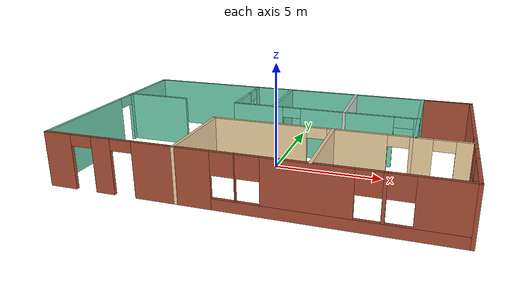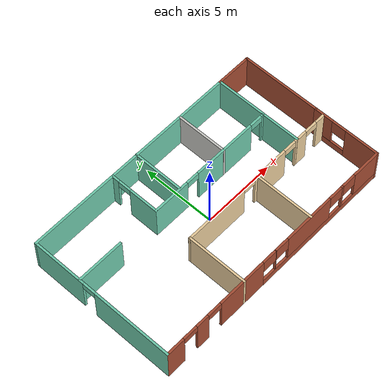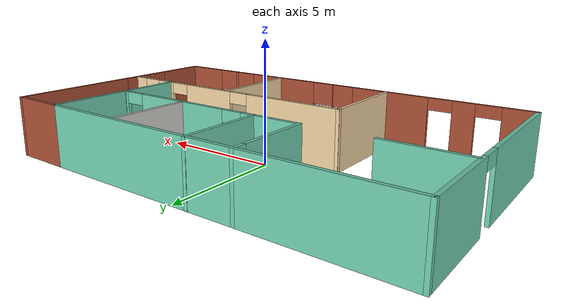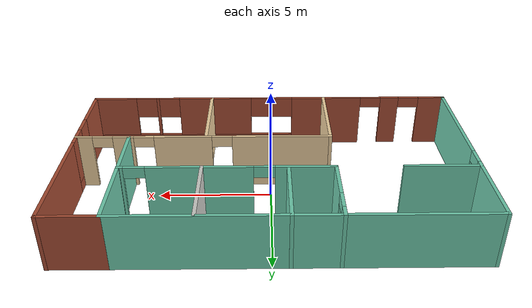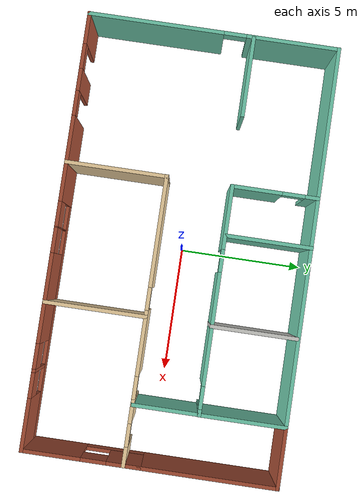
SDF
<?xml version='1.0'?>
<sdf version='1.6'>
  <model name='MyHouse'>
    <link name='Wall_11'>
      <pose frame=''>0 -4.98957 0 0 -0 0</pose>
      <self_collide>0</self_collide>
      <enable_wind>0</enable_wind>
      <kinematic>0</kinematic>
      <visual name='Wall_11_Visual_13'>
        <pose frame=''>-5.04225 0 2.25 0 -0 0</pose>
        <geometry>
          <box>
            <size>1 0.15 0.5</size>
          </box>
        </geometry>
        <material>
          <script>
            <uri>file://media/materials/scripts/gazebo.material</uri>
            <name>Gazebo/Bricks</name>
          </script>
          <ambient>0.435294 0.796078 0.67451 1</ambient>
        </material>
        <meta>
          <layer>0</layer>
        </meta>
        <transparency>0</transparency>
        <cast_shadows>1</cast_shadows>
      </visual>
      <visual name='Wall_11_Visual_6'>
        <pose frame=''>5.58627 0 1.5 0 -0 0</pose>
        <geometry>
          <box>
            <size>0.1334 0.15 2</size>
          </box>
        </geometry>
        <material>
          <script>
            <uri>file://media/materials/scripts/gazebo.material</uri>
            <name>Gazebo/Bricks</name>
          </script>
          <ambient>0.435294 0.796078 0.67451 1</ambient>
        </material>
        <meta>
          <layer>0</layer>
        </meta>
        <transparency>0</transparency>
        <cast_shadows>1</cast_shadows>
      </visual>
      <visual name='Wall_11_Visual_2'>
        <pose frame=''>-2.82171 0 1.25 0 -0 0</pose>
        <geometry>
          <box>
            <size>3.44108 0.15 2.5</size>
          </box>
        </geometry>
        <material>
          <script>
            <uri>file://media/materials/scripts/gazebo.material</uri>
            <name>Gazebo/Bricks</name>
          </script>
          <ambient>0.435294 0.796078 0.67451 1</ambient>
        </material>
        <meta>
          <layer>0</layer>
        </meta>
        <transparency>0</transparency>
        <cast_shadows>1</cast_shadows>
      </visual>
      <visual name='Wall_11_Visual_3'>
        <pose frame=''>3.82441 0 0.25 0 -0 0</pose>
        <geometry>
          <box>
            <size>9.85117 0.15 0.5</size>
          </box>
        </geometry>
        <material>
          <script>
            <uri>file://media/materials/scripts/gazebo.material</uri>
            <name>Gazebo/Bricks</name>
          </script>
          <ambient>0.435294 0.796078 0.67451 1</ambient>
        </material>
        <meta>
          <layer>0</layer>
        </meta>
        <transparency>0</transparency>
        <cast_shadows>1</cast_shadows>
      </visual>
      <visual name='Wall_11_Visual_5'>
        <pose frame=''>2.72964 0 1.5 0 -0 0</pose>
        <geometry>
          <box>
            <size>3.57986 0.15 2</size>
          </box>
        </geometry>
        <material>
          <script>
            <uri>file://media/materials/scripts/gazebo.material</uri>
            <name>Gazebo/Bricks</name>
          </script>
          <ambient>0.435294 0.796078 0.67451 1</ambient>
        </material>
        <meta>
          <layer>0</layer>
        </meta>
        <transparency>0</transparency>
        <cast_shadows>1</cast_shadows>
      </visual>
      <visual name='Wall_11_Visual_4'>
        <pose frame=''>-0.080734 0 1.5 0 -0 0</pose>
        <geometry>
          <box>
            <size>0.040877 0.15 2</size>
          </box>
        </geometry>
        <material>
          <script>
            <uri>file://media/materials/scripts/gazebo.material</uri>
            <name>Gazebo/Bricks</name>
          </script>
          <ambient>0.435294 0.796078 0.67451 1</ambient>
        </material>
        <meta>
          <layer>0</layer>
        </meta>
        <transparency>0</transparency>
        <cast_shadows>1</cast_shadows>
      </visual>
      <visual name='Wall_11_Visual_8'>
        <pose frame=''>-0.601172 0 2 0 -0 0</pose>
        <geometry>
          <box>
            <size>1 0.15 1</size>
          </box>
        </geometry>
        <material>
          <script>
            <uri>file://media/materials/scripts/gazebo.material</uri>
            <name>Gazebo/Bricks</name>
          </script>
          <ambient>0.435294 0.796078 0.67451 1</ambient>
        </material>
        <meta>
          <layer>0</layer>
        </meta>
        <transparency>0</transparency>
        <cast_shadows>1</cast_shadows>
      </visual>
      <visual name='Wall_11_Visual_12'>
        <pose frame=''>-6.93896 0 2.25 0 -0 0</pose>
        <geometry>
          <box>
            <size>1 0.15 0.5</size>
          </box>
        </geometry>
        <material>
          <script>
            <uri>file://media/materials/scripts/gazebo.material</uri>
            <name>Gazebo/Bricks</name>
          </script>
          <ambient>0.435294 0.796078 0.67451 1</ambient>
        </material>
        <meta>
          <layer>0</layer>
        </meta>
        <transparency>0</transparency>
        <cast_shadows>1</cast_shadows>
      </visual>
      <visual name='Wall_11_Visual_11'>
        <pose frame=''>6.15297 0 2 0 -0 0</pose>
        <geometry>
          <box>
            <size>1 0.15 1</size>
          </box>
        </geometry>
        <material>
          <script>
            <uri>file://media/materials/scripts/gazebo.material</uri>
            <name>Gazebo/Bricks</name>
          </script>
          <ambient>0.435294 0.796078 0.67451 1</ambient>
        </material>
        <meta>
          <layer>0</layer>
        </meta>
        <transparency>0</transparency>
        <cast_shadows>1</cast_shadows>
      </visual>
      <visual name='Wall_11_Visual_7'>
        <pose frame=''>7.70148 0 1.5 0 -0 0</pose>
        <geometry>
          <box>
            <size>2.09703 0.15 2</size>
          </box>
        </geometry>
        <material>
          <script>
            <uri>file://media/materials/scripts/gazebo.material</uri>
            <name>Gazebo/Bricks</name>
          </script>
          <ambient>0.435294 0.796078 0.67451 1</ambient>
        </material>
        <meta>
          <layer>0</layer>
        </meta>
        <transparency>0</transparency>
        <cast_shadows>1</cast_shadows>
      </visual>
      <visual name='Wall_11_Visual_9'>
        <pose frame=''>0.439705 0 2 0 -0 0</pose>
        <geometry>
          <box>
            <size>1 0.15 1</size>
          </box>
        </geometry>
        <material>
          <script>
            <uri>file://media/materials/scripts/gazebo.material</uri>
            <name>Gazebo/Bricks</name>
          </script>
          <ambient>0.435294 0.796078 0.67451 1</ambient>
        </material>
        <meta>
          <layer>0</layer>
        </meta>
        <transparency>0</transparency>
        <cast_shadows>1</cast_shadows>
      </visual>
      <visual name='Wall_11_Visual_1'>
        <pose frame=''>-5.9906 0 1.25 0 -0 0</pose>
        <geometry>
          <box>
            <size>0.89671 0.15 2.5</size>
          </box>
        </geometry>
        <material>
          <script>
            <uri>file://media/materials/scripts/gazebo.material</uri>
            <name>Gazebo/Bricks</name>
          </script>
          <ambient>0.435294 0.796078 0.67451 1</ambient>
        </material>
        <meta>
          <layer>0</layer>
        </meta>
        <transparency>0</transparency>
        <cast_shadows>1</cast_shadows>
      </visual>
      <visual name='Wall_11_Visual_0'>
        <pose frame=''>-8.09448 0 1.25 0 -0 0</pose>
        <geometry>
          <box>
            <size>1.31104 0.15 2.5</size>
          </box>
        </geometry>
        <material>
          <script>
            <uri>file://media/materials/scripts/gazebo.material</uri>
            <name>Gazebo/Bricks</name>
          </script>
          <ambient>0.435294 0.796078 0.67451 1</ambient>
        </material>
        <meta>
          <layer>0</layer>
        </meta>
        <transparency>0</transparency>
        <cast_shadows>1</cast_shadows>
      </visual>
      <visual name='Wall_11_Visual_10'>
        <pose frame=''>5.01957 0 2 0 -0 0</pose>
        <geometry>
          <box>
            <size>1 0.15 1</size>
          </box>
        </geometry>
        <material>
          <script>
            <uri>file://media/materials/scripts/gazebo.material</uri>
            <name>Gazebo/Bricks</name>
          </script>
          <ambient>0.435294 0.796078 0.67451 1</ambient>
        </material>
        <meta>
          <layer>0</layer>
        </meta>
        <transparency>0</transparency>
        <cast_shadows>1</cast_shadows>
      </visual>
      <collision name='Wall_11_Collision_12'>
        <laser_retro>0</laser_retro>
        <max_contacts>10</max_contacts>
        <pose frame=''>-6.93896 0 2.25 0 -0 0</pose>
        <geometry>
          <box>
            <size>1 0.15 0.5</size>
          </box>
        </geometry>
        <surface>
          <friction>
            <ode>
              <mu>1</mu>
              <mu2>1</mu2>
              <fdir1>0 0 0</fdir1>
              <slip1>0</slip1>
              <slip2>0</slip2>
            </ode>
            <torsional>
              <coefficient>1</coefficient>
              <patch_radius>0</patch_radius>
              <surface_radius>0</surface_radius>
              <use_patch_radius>1</use_patch_radius>
              <ode>
                <slip>0</slip>
              </ode>
            </torsional>
          </friction>
          <bounce>
            <restitution_coefficient>0</restitution_coefficient>
            <threshold>1e+06</threshold>
          </bounce>
          <contact>
            <collide_without_contact>0</collide_without_contact>
            <collide_without_contact_bitmask>1</collide_without_contact_bitmask>
            <collide_bitmask>1</collide_bitmask>
            <ode>
              <soft_cfm>0</soft_cfm>
              <soft_erp>0.2</soft_erp>
              <kp>1e+13</kp>
              <kd>1</kd>
              <max_vel>0.01</max_vel>
              <min_depth>0</min_depth>
            </ode>
            <bullet>
              <split_impulse>1</split_impulse>
              <split_impulse_penetration_threshold>-0.01</split_impulse_penetration_threshold>
              <soft_cfm>0</soft_cfm>
              <soft_erp>0.2</soft_erp>
              <kp>1e+13</kp>
              <kd>1</kd>
            </bullet>
          </contact>
        </surface>
      </collision>
      <collision name='Wall_11_Collision_7'>
        <laser_retro>0</laser_retro>
        <max_contacts>10</max_contacts>
        <pose frame=''>7.70148 0 1.5 0 -0 0</pose>
        <geometry>
          <box>
            <size>2.09703 0.15 2</size>
          </box>
        </geometry>
        <surface>
          <friction>
            <ode>
              <mu>1</mu>
              <mu2>1</mu2>
              <fdir1>0 0 0</fdir1>
              <slip1>0</slip1>
              <slip2>0</slip2>
            </ode>
            <torsional>
              <coefficient>1</coefficient>
              <patch_radius>0</patch_radius>
              <surface_radius>0</surface_radius>
              <use_patch_radius>1</use_patch_radius>
              <ode>
                <slip>0</slip>
              </ode>
            </torsional>
          </friction>
          <bounce>
            <restitution_coefficient>0</restitution_coefficient>
            <threshold>1e+06</threshold>
          </bounce>
          <contact>
            <collide_without_contact>0</collide_without_contact>
            <collide_without_contact_bitmask>1</collide_without_contact_bitmask>
            <collide_bitmask>1</collide_bitmask>
            <ode>
              <soft_cfm>0</soft_cfm>
              <soft_erp>0.2</soft_erp>
              <kp>1e+13</kp>
              <kd>1</kd>
              <max_vel>0.01</max_vel>
              <min_depth>0</min_depth>
            </ode>
            <bullet>
              <split_impulse>1</split_impulse>
              <split_impulse_penetration_threshold>-0.01</split_impulse_penetration_threshold>
              <soft_cfm>0</soft_cfm>
              <soft_erp>0.2</soft_erp>
              <kp>1e+13</kp>
              <kd>1</kd>
            </bullet>
          </contact>
        </surface>
      </collision>
      <collision name='Wall_11_Collision_2'>
        <laser_retro>0</laser_retro>
        <max_contacts>10</max_contacts>
        <pose frame=''>-2.82171 0 1.25 0 -0 0</pose>
        <geometry>
          <box>
            <size>3.44108 0.15 2.5</size>
          </box>
        </geometry>
        <surface>
          <friction>
            <ode>
              <mu>1</mu>
              <mu2>1</mu2>
              <fdir1>0 0 0</fdir1>
              <slip1>0</slip1>
              <slip2>0</slip2>
            </ode>
            <torsional>
              <coefficient>1</coefficient>
              <patch_radius>0</patch_radius>
              <surface_radius>0</surface_radius>
              <use_patch_radius>1</use_patch_radius>
              <ode>
                <slip>0</slip>
              </ode>
            </torsional>
          </friction>
          <bounce>
            <restitution_coefficient>0</restitution_coefficient>
            <threshold>1e+06</threshold>
          </bounce>
          <contact>
            <collide_without_contact>0</collide_without_contact>
            <collide_without_contact_bitmask>1</collide_without_contact_bitmask>
            <collide_bitmask>1</collide_bitmask>
            <ode>
              <soft_cfm>0</soft_cfm>
              <soft_erp>0.2</soft_erp>
              <kp>1e+13</kp>
              <kd>1</kd>
              <max_vel>0.01</max_vel>
              <min_depth>0</min_depth>
            </ode>
            <bullet>
              <split_impulse>1</split_impulse>
              <split_impulse_penetration_threshold>-0.01</split_impulse_penetration_threshold>
              <soft_cfm>0</soft_cfm>
              <soft_erp>0.2</soft_erp>
              <kp>1e+13</kp>
              <kd>1</kd>
            </bullet>
          </contact>
        </surface>
      </collision>
      <collision name='Wall_11_Collision_8'>
        <laser_retro>0</laser_retro>
        <max_contacts>10</max_contacts>
        <pose frame=''>-0.601172 0 2 0 -0 0</pose>
        <geometry>
          <box>
            <size>1 0.15 1</size>
          </box>
        </geometry>
        <surface>
          <friction>
            <ode>
              <mu>1</mu>
              <mu2>1</mu2>
              <fdir1>0 0 0</fdir1>
              <slip1>0</slip1>
              <slip2>0</slip2>
            </ode>
            <torsional>
              <coefficient>1</coefficient>
              <patch_radius>0</patch_radius>
              <surface_radius>0</surface_radius>
              <use_patch_radius>1</use_patch_radius>
              <ode>
                <slip>0</slip>
              </ode>
            </torsional>
          </friction>
          <bounce>
            <restitution_coefficient>0</restitution_coefficient>
            <threshold>1e+06</threshold>
          </bounce>
          <contact>
            <collide_without_contact>0</collide_without_contact>
            <collide_without_contact_bitmask>1</collide_without_contact_bitmask>
            <collide_bitmask>1</collide_bitmask>
            <ode>
              <soft_cfm>0</soft_cfm>
              <soft_erp>0.2</soft_erp>
              <kp>1e+13</kp>
              <kd>1</kd>
              <max_vel>0.01</max_vel>
              <min_depth>0</min_depth>
            </ode>
            <bullet>
              <split_impulse>1</split_impulse>
              <split_impulse_penetration_threshold>-0.01</split_impulse_penetration_threshold>
              <soft_cfm>0</soft_cfm>
              <soft_erp>0.2</soft_erp>
              <kp>1e+13</kp>
              <kd>1</kd>
            </bullet>
          </contact>
        </surface>
      </collision>
      <collision name='Wall_11_Collision_13'>
        <laser_retro>0</laser_retro>
        <max_contacts>10</max_contacts>
        <pose frame=''>-5.04225 0 2.25 0 -0 0</pose>
        <geometry>
          <box>
            <size>1 0.15 0.5</size>
          </box>
        </geometry>
        <surface>
          <friction>
            <ode>
              <mu>1</mu>
              <mu2>1</mu2>
              <fdir1>0 0 0</fdir1>
              <slip1>0</slip1>
              <slip2>0</slip2>
            </ode>
            <torsional>
              <coefficient>1</coefficient>
              <patch_radius>0</patch_radius>
              <surface_radius>0</surface_radius>
              <use_patch_radius>1</use_patch_radius>
              <ode>
                <slip>0</slip>
              </ode>
            </torsional>
          </friction>
          <bounce>
            <restitution_coefficient>0</restitution_coefficient>
            <threshold>1e+06</threshold>
          </bounce>
          <contact>
            <collide_without_contact>0</collide_without_contact>
            <collide_without_contact_bitmask>1</collide_without_contact_bitmask>
            <collide_bitmask>1</collide_bitmask>
            <ode>
              <soft_cfm>0</soft_cfm>
              <soft_erp>0.2</soft_erp>
              <kp>1e+13</kp>
              <kd>1</kd>
              <max_vel>0.01</max_vel>
              <min_depth>0</min_depth>
            </ode>
            <bullet>
              <split_impulse>1</split_impulse>
              <split_impulse_penetration_threshold>-0.01</split_impulse_penetration_threshold>
              <soft_cfm>0</soft_cfm>
              <soft_erp>0.2</soft_erp>
              <kp>1e+13</kp>
              <kd>1</kd>
            </bullet>
          </contact>
        </surface>
      </collision>
      <collision name='Wall_11_Collision_6'>
        <laser_retro>0</laser_retro>
        <max_contacts>10</max_contacts>
        <pose frame=''>5.58627 0 1.5 0 -0 0</pose>
        <geometry>
          <box>
            <size>0.1334 0.15 2</size>
          </box>
        </geometry>
        <surface>
          <friction>
            <ode>
              <mu>1</mu>
              <mu2>1</mu2>
              <fdir1>0 0 0</fdir1>
              <slip1>0</slip1>
              <slip2>0</slip2>
            </ode>
            <torsional>
              <coefficient>1</coefficient>
              <patch_radius>0</patch_radius>
              <surface_radius>0</surface_radius>
              <use_patch_radius>1</use_patch_radius>
              <ode>
                <slip>0</slip>
              </ode>
            </torsional>
          </friction>
          <bounce>
            <restitution_coefficient>0</restitution_coefficient>
            <threshold>1e+06</threshold>
          </bounce>
          <contact>
            <collide_without_contact>0</collide_without_contact>
            <collide_without_contact_bitmask>1</collide_without_contact_bitmask>
            <collide_bitmask>1</collide_bitmask>
            <ode>
              <soft_cfm>0</soft_cfm>
              <soft_erp>0.2</soft_erp>
              <kp>1e+13</kp>
              <kd>1</kd>
              <max_vel>0.01</max_vel>
              <min_depth>0</min_depth>
            </ode>
            <bullet>
              <split_impulse>1</split_impulse>
              <split_impulse_penetration_threshold>-0.01</split_impulse_penetration_threshold>
              <soft_cfm>0</soft_cfm>
              <soft_erp>0.2</soft_erp>
              <kp>1e+13</kp>
              <kd>1</kd>
            </bullet>
          </contact>
        </surface>
      </collision>
      <collision name='Wall_11_Collision_3'>
        <laser_retro>0</laser_retro>
        <max_contacts>10</max_contacts>
        <pose frame=''>3.82441 0 0.25 0 -0 0</pose>
        <geometry>
          <box>
            <size>9.85117 0.15 0.5</size>
          </box>
        </geometry>
        <surface>
          <friction>
            <ode>
              <mu>1</mu>
              <mu2>1</mu2>
              <fdir1>0 0 0</fdir1>
              <slip1>0</slip1>
              <slip2>0</slip2>
            </ode>
            <torsional>
              <coefficient>1</coefficient>
              <patch_radius>0</patch_radius>
              <surface_radius>0</surface_radius>
              <use_patch_radius>1</use_patch_radius>
              <ode>
                <slip>0</slip>
              </ode>
            </torsional>
          </friction>
          <bounce>
            <restitution_coefficient>0</restitution_coefficient>
            <threshold>1e+06</threshold>
          </bounce>
          <contact>
            <collide_without_contact>0</collide_without_contact>
            <collide_without_contact_bitmask>1</collide_without_contact_bitmask>
            <collide_bitmask>1</collide_bitmask>
            <ode>
              <soft_cfm>0</soft_cfm>
              <soft_erp>0.2</soft_erp>
              <kp>1e+13</kp>
              <kd>1</kd>
              <max_vel>0.01</max_vel>
              <min_depth>0</min_depth>
            </ode>
            <bullet>
              <split_impulse>1</split_impulse>
              <split_impulse_penetration_threshold>-0.01</split_impulse_penetration_threshold>
              <soft_cfm>0</soft_cfm>
              <soft_erp>0.2</soft_erp>
              <kp>1e+13</kp>
              <kd>1</kd>
            </bullet>
          </contact>
        </surface>
      </collision>
      <collision name='Wall_11_Collision_10'>
        <laser_retro>0</laser_retro>
        <max_contacts>10</max_contacts>
        <pose frame=''>5.01957 0 2 0 -0 0</pose>
        <geometry>
          <box>
            <size>1 0.15 1</size>
          </box>
        </geometry>
        <surface>
          <friction>
            <ode>
              <mu>1</mu>
              <mu2>1</mu2>
              <fdir1>0 0 0</fdir1>
              <slip1>0</slip1>
              <slip2>0</slip2>
            </ode>
            <torsional>
              <coefficient>1</coefficient>
              <patch_radius>0</patch_radius>
              <surface_radius>0</surface_radius>
              <use_patch_radius>1</use_patch_radius>
              <ode>
                <slip>0</slip>
              </ode>
            </torsional>
          </friction>
          <bounce>
            <restitution_coefficient>0</restitution_coefficient>
            <threshold>1e+06</threshold>
          </bounce>
          <contact>
            <collide_without_contact>0</collide_without_contact>
            <collide_without_contact_bitmask>1</collide_without_contact_bitmask>
            <collide_bitmask>1</collide_bitmask>
            <ode>
              <soft_cfm>0</soft_cfm>
              <soft_erp>0.2</soft_erp>
              <kp>1e+13</kp>
              <kd>1</kd>
              <max_vel>0.01</max_vel>
              <min_depth>0</min_depth>
            </ode>
            <bullet>
              <split_impulse>1</split_impulse>
              <split_impulse_penetration_threshold>-0.01</split_impulse_penetration_threshold>
              <soft_cfm>0</soft_cfm>
              <soft_erp>0.2</soft_erp>
              <kp>1e+13</kp>
              <kd>1</kd>
            </bullet>
          </contact>
        </surface>
      </collision>
      <collision name='Wall_11_Collision_4'>
        <laser_retro>0</laser_retro>
        <max_contacts>10</max_contacts>
        <pose frame=''>-0.080734 0 1.5 0 -0 0</pose>
        <geometry>
          <box>
            <size>0.040877 0.15 2</size>
          </box>
        </geometry>
        <surface>
          <friction>
            <ode>
              <mu>1</mu>
              <mu2>1</mu2>
              <fdir1>0 0 0</fdir1>
              <slip1>0</slip1>
              <slip2>0</slip2>
            </ode>
            <torsional>
              <coefficient>1</coefficient>
              <patch_radius>0</patch_radius>
              <surface_radius>0</surface_radius>
              <use_patch_radius>1</use_patch_radius>
              <ode>
                <slip>0</slip>
              </ode>
            </torsional>
          </friction>
          <bounce>
            <restitution_coefficient>0</restitution_coefficient>
            <threshold>1e+06</threshold>
          </bounce>
          <contact>
            <collide_without_contact>0</collide_without_contact>
            <collide_without_contact_bitmask>1</collide_without_contact_bitmask>
            <collide_bitmask>1</collide_bitmask>
            <ode>
              <soft_cfm>0</soft_cfm>
              <soft_erp>0.2</soft_erp>
              <kp>1e+13</kp>
              <kd>1</kd>
              <max_vel>0.01</max_vel>
              <min_depth>0</min_depth>
            </ode>
            <bullet>
              <split_impulse>1</split_impulse>
              <split_impulse_penetration_threshold>-0.01</split_impulse_penetration_threshold>
              <soft_cfm>0</soft_cfm>
              <soft_erp>0.2</soft_erp>
              <kp>1e+13</kp>
              <kd>1</kd>
            </bullet>
          </contact>
        </surface>
      </collision>
      <collision name='Wall_11_Collision_5'>
        <laser_retro>0</laser_retro>
        <max_contacts>10</max_contacts>
        <pose frame=''>2.72964 0 1.5 0 -0 0</pose>
        <geometry>
          <box>
            <size>3.57986 0.15 2</size>
          </box>
        </geometry>
        <surface>
          <friction>
            <ode>
              <mu>1</mu>
              <mu2>1</mu2>
              <fdir1>0 0 0</fdir1>
              <slip1>0</slip1>
              <slip2>0</slip2>
            </ode>
            <torsional>
              <coefficient>1</coefficient>
              <patch_radius>0</patch_radius>
              <surface_radius>0</surface_radius>
              <use_patch_radius>1</use_patch_radius>
              <ode>
                <slip>0</slip>
              </ode>
            </torsional>
          </friction>
          <bounce>
            <restitution_coefficient>0</restitution_coefficient>
            <threshold>1e+06</threshold>
          </bounce>
          <contact>
            <collide_without_contact>0</collide_without_contact>
            <collide_without_contact_bitmask>1</collide_without_contact_bitmask>
            <collide_bitmask>1</collide_bitmask>
            <ode>
              <soft_cfm>0</soft_cfm>
              <soft_erp>0.2</soft_erp>
              <kp>1e+13</kp>
              <kd>1</kd>
              <max_vel>0.01</max_vel>
              <min_depth>0</min_depth>
            </ode>
            <bullet>
              <split_impulse>1</split_impulse>
              <split_impulse_penetration_threshold>-0.01</split_impulse_penetration_threshold>
              <soft_cfm>0</soft_cfm>
              <soft_erp>0.2</soft_erp>
              <kp>1e+13</kp>
              <kd>1</kd>
            </bullet>
          </contact>
        </surface>
      </collision>
      <collision name='Wall_11_Collision_9'>
        <laser_retro>0</laser_retro>
        <max_contacts>10</max_contacts>
        <pose frame=''>0.439705 0 2 0 -0 0</pose>
        <geometry>
          <box>
            <size>1 0.15 1</size>
          </box>
        </geometry>
        <surface>
          <friction>
            <ode>
              <mu>1</mu>
              <mu2>1</mu2>
              <fdir1>0 0 0</fdir1>
              <slip1>0</slip1>
              <slip2>0</slip2>
            </ode>
            <torsional>
              <coefficient>1</coefficient>
              <patch_radius>0</patch_radius>
              <surface_radius>0</surface_radius>
              <use_patch_radius>1</use_patch_radius>
              <ode>
                <slip>0</slip>
              </ode>
            </torsional>
          </friction>
          <bounce>
            <restitution_coefficient>0</restitution_coefficient>
            <threshold>1e+06</threshold>
          </bounce>
          <contact>
            <collide_without_contact>0</collide_without_contact>
            <collide_without_contact_bitmask>1</collide_without_contact_bitmask>
            <collide_bitmask>1</collide_bitmask>
            <ode>
              <soft_cfm>0</soft_cfm>
              <soft_erp>0.2</soft_erp>
              <kp>1e+13</kp>
              <kd>1</kd>
              <max_vel>0.01</max_vel>
              <min_depth>0</min_depth>
            </ode>
            <bullet>
              <split_impulse>1</split_impulse>
              <split_impulse_penetration_threshold>-0.01</split_impulse_penetration_threshold>
              <soft_cfm>0</soft_cfm>
              <soft_erp>0.2</soft_erp>
              <kp>1e+13</kp>
              <kd>1</kd>
            </bullet>
          </contact>
        </surface>
      </collision>
      <collision name='Wall_11_Collision_1'>
        <laser_retro>0</laser_retro>
        <max_contacts>10</max_contacts>
        <pose frame=''>-5.9906 0 1.25 0 -0 0</pose>
        <geometry>
          <box>
            <size>0.89671 0.15 2.5</size>
          </box>
        </geometry>
        <surface>
          <friction>
            <ode>
              <mu>1</mu>
              <mu2>1</mu2>
              <fdir1>0 0 0</fdir1>
              <slip1>0</slip1>
              <slip2>0</slip2>
            </ode>
            <torsional>
              <coefficient>1</coefficient>
              <patch_radius>0</patch_radius>
              <surface_radius>0</surface_radius>
              <use_patch_radius>1</use_patch_radius>
              <ode>
                <slip>0</slip>
              </ode>
            </torsional>
          </friction>
          <bounce>
            <restitution_coefficient>0</restitution_coefficient>
            <threshold>1e+06</threshold>
          </bounce>
          <contact>
            <collide_without_contact>0</collide_without_contact>
            <collide_without_contact_bitmask>1</collide_without_contact_bitmask>
            <collide_bitmask>1</collide_bitmask>
            <ode>
              <soft_cfm>0</soft_cfm>
              <soft_erp>0.2</soft_erp>
              <kp>1e+13</kp>
              <kd>1</kd>
              <max_vel>0.01</max_vel>
              <min_depth>0</min_depth>
            </ode>
            <bullet>
              <split_impulse>1</split_impulse>
              <split_impulse_penetration_threshold>-0.01</split_impulse_penetration_threshold>
              <soft_cfm>0</soft_cfm>
              <soft_erp>0.2</soft_erp>
              <kp>1e+13</kp>
              <kd>1</kd>
            </bullet>
          </contact>
        </surface>
      </collision>
      <collision name='Wall_11_Collision_0'>
        <laser_retro>0</laser_retro>
        <max_contacts>10</max_contacts>
        <pose frame=''>-8.09448 0 1.25 0 -0 0</pose>
        <geometry>
          <box>
            <size>1.31104 0.15 2.5</size>
          </box>
        </geometry>
        <surface>
          <friction>
            <ode>
              <mu>1</mu>
              <mu2>1</mu2>
              <fdir1>0 0 0</fdir1>
              <slip1>0</slip1>
              <slip2>0</slip2>
            </ode>
            <torsional>
              <coefficient>1</coefficient>
              <patch_radius>0</patch_radius>
              <surface_radius>0</surface_radius>
              <use_patch_radius>1</use_patch_radius>
              <ode>
                <slip>0</slip>
              </ode>
            </torsional>
          </friction>
          <bounce>
            <restitution_coefficient>0</restitution_coefficient>
            <threshold>1e+06</threshold>
          </bounce>
          <contact>
            <collide_without_contact>0</collide_without_contact>
            <collide_without_contact_bitmask>1</collide_without_contact_bitmask>
            <collide_bitmask>1</collide_bitmask>
            <ode>
              <soft_cfm>0</soft_cfm>
              <soft_erp>0.2</soft_erp>
              <kp>1e+13</kp>
              <kd>1</kd>
              <max_vel>0.01</max_vel>
              <min_depth>0</min_depth>
            </ode>
            <bullet>
              <split_impulse>1</split_impulse>
              <split_impulse_penetration_threshold>-0.01</split_impulse_penetration_threshold>
              <soft_cfm>0</soft_cfm>
              <soft_erp>0.2</soft_erp>
              <kp>1e+13</kp>
              <kd>1</kd>
            </bullet>
          </contact>
        </surface>
      </collision>
      <collision name='Wall_11_Collision_11'>
        <laser_retro>0</laser_retro>
        <max_contacts>10</max_contacts>
        <pose frame=''>6.15297 0 2 0 -0 0</pose>
        <geometry>
          <box>
            <size>1 0.15 1</size>
          </box>
        </geometry>
        <surface>
          <friction>
            <ode>
              <mu>1</mu>
              <mu2>1</mu2>
              <fdir1>0 0 0</fdir1>
              <slip1>0</slip1>
              <slip2>0</slip2>
            </ode>
            <torsional>
              <coefficient>1</coefficient>
              <patch_radius>0</patch_radius>
              <surface_radius>0</surface_radius>
              <use_patch_radius>1</use_patch_radius>
              <ode>
                <slip>0</slip>
              </ode>
            </torsional>
          </friction>
          <bounce>
            <restitution_coefficient>0</restitution_coefficient>
            <threshold>1e+06</threshold>
          </bounce>
          <contact>
            <collide_without_contact>0</collide_without_contact>
            <collide_without_contact_bitmask>1</collide_without_contact_bitmask>
            <collide_bitmask>1</collide_bitmask>
            <ode>
              <soft_cfm>0</soft_cfm>
              <soft_erp>0.2</soft_erp>
              <kp>1e+13</kp>
              <kd>1</kd>
              <max_vel>0.01</max_vel>
              <min_depth>0</min_depth>
            </ode>
            <bullet>
              <split_impulse>1</split_impulse>
              <split_impulse_penetration_threshold>-0.01</split_impulse_penetration_threshold>
              <soft_cfm>0</soft_cfm>
              <soft_erp>0.2</soft_erp>
              <kp>1e+13</kp>
              <kd>1</kd>
            </bullet>
          </contact>
        </surface>
      </collision>
    </link>
    <link name='Wall_18'>
      <pose frame=''>-8.675 0.010434 0 0 0 -1.5708</pose>
      <self_collide>0</self_collide>
      <enable_wind>0</enable_wind>
      <kinematic>0</kinematic>
      <visual name='Wall_18_Visual_2'>
        <pose frame=''>-0.852841 0 2.25 0 -0 0</pose>
        <geometry>
          <box>
            <size>0.9 0.15 0.5</size>
          </box>
        </geometry>
        <material>
          <script>
            <uri>file://media/materials/scripts/gazebo.material</uri>
            <name>Gazebo/Grey</name>
          </script>
          <ambient>0.435294 0.796078 0.67451 1</ambient>
        </material>
        <meta>
          <layer>0</layer>
        </meta>
        <transparency>0</transparency>
        <cast_shadows>1</cast_shadows>
      </visual>
      <visual name='Wall_18_Visual_1'>
        <pose frame=''>2.33608 0 1.25 0 -0 0</pose>
        <geometry>
          <box>
            <size>5.47784 0.15 2.5</size>
          </box>
        </geometry>
        <material>
          <script>
            <uri>file://media/materials/scripts/gazebo.material</uri>
            <name>Gazebo/Grey</name>
          </script>
          <ambient>0.435294 0.796078 0.67451 1</ambient>
        </material>
        <meta>
          <layer>0</layer>
        </meta>
        <transparency>0</transparency>
        <cast_shadows>1</cast_shadows>
      </visual>
      <visual name='Wall_18_Visual_0'>
        <pose frame=''>-3.18892 0 1.25 0 -0 0</pose>
        <geometry>
          <box>
            <size>3.77216 0.15 2.5</size>
          </box>
        </geometry>
        <material>
          <script>
            <uri>file://media/materials/scripts/gazebo.material</uri>
            <name>Gazebo/Grey</name>
          </script>
          <ambient>0.435294 0.796078 0.67451 1</ambient>
        </material>
        <meta>
          <layer>0</layer>
        </meta>
        <transparency>0</transparency>
        <cast_shadows>1</cast_shadows>
      </visual>
      <collision name='Wall_18_Collision_2'>
        <laser_retro>0</laser_retro>
        <max_contacts>10</max_contacts>
        <pose frame=''>-0.852841 0 2.25 0 -0 0</pose>
        <geometry>
          <box>
            <size>0.9 0.15 0.5</size>
          </box>
        </geometry>
        <surface>
          <friction>
            <ode>
              <mu>1</mu>
              <mu2>1</mu2>
              <fdir1>0 0 0</fdir1>
              <slip1>0</slip1>
              <slip2>0</slip2>
            </ode>
            <torsional>
              <coefficient>1</coefficient>
              <patch_radius>0</patch_radius>
              <surface_radius>0</surface_radius>
              <use_patch_radius>1</use_patch_radius>
              <ode>
                <slip>0</slip>
              </ode>
            </torsional>
          </friction>
          <bounce>
            <restitution_coefficient>0</restitution_coefficient>
            <threshold>1e+06</threshold>
          </bounce>
          <contact>
            <collide_without_contact>0</collide_without_contact>
            <collide_without_contact_bitmask>1</collide_without_contact_bitmask>
            <collide_bitmask>1</collide_bitmask>
            <ode>
              <soft_cfm>0</soft_cfm>
              <soft_erp>0.2</soft_erp>
              <kp>1e+13</kp>
              <kd>1</kd>
              <max_vel>0.01</max_vel>
              <min_depth>0</min_depth>
            </ode>
            <bullet>
              <split_impulse>1</split_impulse>
              <split_impulse_penetration_threshold>-0.01</split_impulse_penetration_threshold>
              <soft_cfm>0</soft_cfm>
              <soft_erp>0.2</soft_erp>
              <kp>1e+13</kp>
              <kd>1</kd>
            </bullet>
          </contact>
        </surface>
      </collision>
      <collision name='Wall_18_Collision_1'>
        <laser_retro>0</laser_retro>
        <max_contacts>10</max_contacts>
        <pose frame=''>2.33608 0 1.25 0 -0 0</pose>
        <geometry>
          <box>
            <size>5.47784 0.15 2.5</size>
          </box>
        </geometry>
        <surface>
          <friction>
            <ode>
              <mu>1</mu>
              <mu2>1</mu2>
              <fdir1>0 0 0</fdir1>
              <slip1>0</slip1>
              <slip2>0</slip2>
            </ode>
            <torsional>
              <coefficient>1</coefficient>
              <patch_radius>0</patch_radius>
              <surface_radius>0</surface_radius>
              <use_patch_radius>1</use_patch_radius>
              <ode>
                <slip>0</slip>
              </ode>
            </torsional>
          </friction>
          <bounce>
            <restitution_coefficient>0</restitution_coefficient>
            <threshold>1e+06</threshold>
          </bounce>
          <contact>
            <collide_without_contact>0</collide_without_contact>
            <collide_without_contact_bitmask>1</collide_without_contact_bitmask>
            <collide_bitmask>1</collide_bitmask>
            <ode>
              <soft_cfm>0</soft_cfm>
              <soft_erp>0.2</soft_erp>
              <kp>1e+13</kp>
              <kd>1</kd>
              <max_vel>0.01</max_vel>
              <min_depth>0</min_depth>
            </ode>
            <bullet>
              <split_impulse>1</split_impulse>
              <split_impulse_penetration_threshold>-0.01</split_impulse_penetration_threshold>
              <soft_cfm>0</soft_cfm>
              <soft_erp>0.2</soft_erp>
              <kp>1e+13</kp>
              <kd>1</kd>
            </bullet>
          </contact>
        </surface>
      </collision>
      <collision name='Wall_18_Collision_0'>
        <laser_retro>0</laser_retro>
        <max_contacts>10</max_contacts>
        <pose frame=''>-3.18892 0 1.25 0 -0 0</pose>
        <geometry>
          <box>
            <size>3.77216 0.15 2.5</size>
          </box>
        </geometry>
        <surface>
          <friction>
            <ode>
              <mu>1</mu>
              <mu2>1</mu2>
              <fdir1>0 0 0</fdir1>
              <slip1>0</slip1>
              <slip2>0</slip2>
            </ode>
            <torsional>
              <coefficient>1</coefficient>
              <patch_radius>0</patch_radius>
              <surface_radius>0</surface_radius>
              <use_patch_radius>1</use_patch_radius>
              <ode>
                <slip>0</slip>
              </ode>
            </torsional>
          </friction>
          <bounce>
            <restitution_coefficient>0</restitution_coefficient>
            <threshold>1e+06</threshold>
          </bounce>
          <contact>
            <collide_without_contact>0</collide_without_contact>
            <collide_without_contact_bitmask>1</collide_without_contact_bitmask>
            <collide_bitmask>1</collide_bitmask>
            <ode>
              <soft_cfm>0</soft_cfm>
              <soft_erp>0.2</soft_erp>
              <kp>1e+13</kp>
              <kd>1</kd>
              <max_vel>0.01</max_vel>
              <min_depth>0</min_depth>
            </ode>
            <bullet>
              <split_impulse>1</split_impulse>
              <split_impulse_penetration_threshold>-0.01</split_impulse_penetration_threshold>
              <soft_cfm>0</soft_cfm>
              <soft_erp>0.2</soft_erp>
              <kp>1e+13</kp>
              <kd>1</kd>
            </bullet>
          </contact>
        </surface>
      </collision>
    </link>
    <link name='Wall_23'>
      <pose frame=''>-2.675 3.31043 0 0 0 -1.5708</pose>
      <self_collide>0</self_collide>
      <enable_wind>0</enable_wind>
      <kinematic>0</kinematic>
      <visual name='Wall_23_Visual_1'>
        <pose frame=''>0.744603 0 1.25 0 -0 0</pose>
        <geometry>
          <box>
            <size>2.06079 0.15 2.5</size>
          </box>
        </geometry>
        <material>
          <script>
            <uri>file://media/materials/scripts/gazebo.material</uri>
            <name>Gazebo/Grey</name>
          </script>
          <ambient>0.435294 0.796078 0.67451 1</ambient>
        </material>
        <meta>
          <layer>0</layer>
        </meta>
        <transparency>0</transparency>
        <cast_shadows>1</cast_shadows>
      </visual>
      <visual name='Wall_23_Visual_2'>
        <pose frame=''>-0.735794 0 2.25 0 -0 0</pose>
        <geometry>
          <box>
            <size>0.9 0.15 0.5</size>
          </box>
        </geometry>
        <material>
          <script>
            <uri>file://media/materials/scripts/gazebo.material</uri>
            <name>Gazebo/Grey</name>
          </script>
          <ambient>0.435294 0.796078 0.67451 1</ambient>
        </material>
        <meta>
          <layer>0</layer>
        </meta>
        <transparency>0</transparency>
        <cast_shadows>1</cast_shadows>
      </visual>
      <visual name='Wall_23_Visual_0'>
        <pose frame=''>-1.4804 0 1.25 0 -0 0</pose>
        <geometry>
          <box>
            <size>0.589206 0.15 2.5</size>
          </box>
        </geometry>
        <material>
          <script>
            <uri>file://media/materials/scripts/gazebo.material</uri>
            <name>Gazebo/Grey</name>
          </script>
          <ambient>0.435294 0.796078 0.67451 1</ambient>
        </material>
        <meta>
          <layer>0</layer>
        </meta>
        <transparency>0</transparency>
        <cast_shadows>1</cast_shadows>
      </visual>
      <collision name='Wall_23_Collision_1'>
        <laser_retro>0</laser_retro>
        <max_contacts>10</max_contacts>
        <pose frame=''>0.744603 0 1.25 0 -0 0</pose>
        <geometry>
          <box>
            <size>2.06079 0.15 2.5</size>
          </box>
        </geometry>
        <surface>
          <friction>
            <ode>
              <mu>1</mu>
              <mu2>1</mu2>
              <fdir1>0 0 0</fdir1>
              <slip1>0</slip1>
              <slip2>0</slip2>
            </ode>
            <torsional>
              <coefficient>1</coefficient>
              <patch_radius>0</patch_radius>
              <surface_radius>0</surface_radius>
              <use_patch_radius>1</use_patch_radius>
              <ode>
                <slip>0</slip>
              </ode>
            </torsional>
          </friction>
          <bounce>
            <restitution_coefficient>0</restitution_coefficient>
            <threshold>1e+06</threshold>
          </bounce>
          <contact>
            <collide_without_contact>0</collide_without_contact>
            <collide_without_contact_bitmask>1</collide_without_contact_bitmask>
            <collide_bitmask>1</collide_bitmask>
            <ode>
              <soft_cfm>0</soft_cfm>
              <soft_erp>0.2</soft_erp>
              <kp>1e+13</kp>
              <kd>1</kd>
              <max_vel>0.01</max_vel>
              <min_depth>0</min_depth>
            </ode>
            <bullet>
              <split_impulse>1</split_impulse>
              <split_impulse_penetration_threshold>-0.01</split_impulse_penetration_threshold>
              <soft_cfm>0</soft_cfm>
              <soft_erp>0.2</soft_erp>
              <kp>1e+13</kp>
              <kd>1</kd>
            </bullet>
          </contact>
        </surface>
      </collision>
      <collision name='Wall_23_Collision_2'>
        <laser_retro>0</laser_retro>
        <max_contacts>10</max_contacts>
        <pose frame=''>-0.735794 0 2.25 0 -0 0</pose>
        <geometry>
          <box>
            <size>0.9 0.15 0.5</size>
          </box>
        </geometry>
        <surface>
          <friction>
            <ode>
              <mu>1</mu>
              <mu2>1</mu2>
              <fdir1>0 0 0</fdir1>
              <slip1>0</slip1>
              <slip2>0</slip2>
            </ode>
            <torsional>
              <coefficient>1</coefficient>
              <patch_radius>0</patch_radius>
              <surface_radius>0</surface_radius>
              <use_patch_radius>1</use_patch_radius>
              <ode>
                <slip>0</slip>
              </ode>
            </torsional>
          </friction>
          <bounce>
            <restitution_coefficient>0</restitution_coefficient>
            <threshold>1e+06</threshold>
          </bounce>
          <contact>
            <collide_without_contact>0</collide_without_contact>
            <collide_without_contact_bitmask>1</collide_without_contact_bitmask>
            <collide_bitmask>1</collide_bitmask>
            <ode>
              <soft_cfm>0</soft_cfm>
              <soft_erp>0.2</soft_erp>
              <kp>1e+13</kp>
              <kd>1</kd>
              <max_vel>0.01</max_vel>
              <min_depth>0</min_depth>
            </ode>
            <bullet>
              <split_impulse>1</split_impulse>
              <split_impulse_penetration_threshold>-0.01</split_impulse_penetration_threshold>
              <soft_cfm>0</soft_cfm>
              <soft_erp>0.2</soft_erp>
              <kp>1e+13</kp>
              <kd>1</kd>
            </bullet>
          </contact>
        </surface>
      </collision>
      <collision name='Wall_23_Collision_0'>
        <laser_retro>0</laser_retro>
        <max_contacts>10</max_contacts>
        <pose frame=''>-1.4804 0 1.25 0 -0 0</pose>
        <geometry>
          <box>
            <size>0.589206 0.15 2.5</size>
          </box>
        </geometry>
        <surface>
          <friction>
            <ode>
              <mu>1</mu>
              <mu2>1</mu2>
              <fdir1>0 0 0</fdir1>
              <slip1>0</slip1>
              <slip2>0</slip2>
            </ode>
            <torsional>
              <coefficient>1</coefficient>
              <patch_radius>0</patch_radius>
              <surface_radius>0</surface_radius>
              <use_patch_radius>1</use_patch_radius>
              <ode>
                <slip>0</slip>
              </ode>
            </torsional>
          </friction>
          <bounce>
            <restitution_coefficient>0</restitution_coefficient>
            <threshold>1e+06</threshold>
          </bounce>
          <contact>
            <collide_without_contact>0</collide_without_contact>
            <collide_without_contact_bitmask>1</collide_without_contact_bitmask>
            <collide_bitmask>1</collide_bitmask>
            <ode>
              <soft_cfm>0</soft_cfm>
              <soft_erp>0.2</soft_erp>
              <kp>1e+13</kp>
              <kd>1</kd>
              <max_vel>0.01</max_vel>
              <min_depth>0</min_depth>
            </ode>
            <bullet>
              <split_impulse>1</split_impulse>
              <split_impulse_penetration_threshold>-0.01</split_impulse_penetration_threshold>
              <soft_cfm>0</soft_cfm>
              <soft_erp>0.2</soft_erp>
              <kp>1e+13</kp>
              <kd>1</kd>
            </bullet>
          </contact>
        </surface>
      </collision>
    </link>
    <link name='Wall_24'>
      <pose frame=''>1.825 1.61043 0 0 -0 0</pose>
      <self_collide>0</self_collide>
      <enable_wind>0</enable_wind>
      <kinematic>0</kinematic>
      <visual name='Wall_24_Visual_4'>
        <pose frame=''>3.83485 0 2.25 0 -0 0</pose>
        <geometry>
          <box>
            <size>0.9 0.15 0.5</size>
          </box>
        </geometry>
        <material>
          <script>
            <uri>file://media/materials/scripts/gazebo.material</uri>
            <name>Gazebo/Grey</name>
          </script>
          <ambient>0.435294 0.796078 0.67451 1</ambient>
        </material>
        <meta>
          <layer>0</layer>
        </meta>
        <transparency>0</transparency>
        <cast_shadows>1</cast_shadows>
      </visual>
      <visual name='Wall_24_Visual_3'>
        <pose frame=''>-1.53839 0 2.25 0 -0 0</pose>
        <geometry>
          <box>
            <size>0.9 0.15 0.5</size>
          </box>
        </geometry>
        <material>
          <script>
            <uri>file://media/materials/scripts/gazebo.material</uri>
            <name>Gazebo/Grey</name>
          </script>
          <ambient>0.435294 0.796078 0.67451 1</ambient>
        </material>
        <meta>
          <layer>0</layer>
        </meta>
        <transparency>0</transparency>
        <cast_shadows>1</cast_shadows>
      </visual>
      <visual name='Wall_24_Visual_0'>
        <pose frame=''>-3.28169 0 1.25 0 -0 0</pose>
        <geometry>
          <box>
            <size>2.58661 0.15 2.5</size>
          </box>
        </geometry>
        <material>
          <script>
            <uri>file://media/materials/scripts/gazebo.material</uri>
            <name>Gazebo/Grey</name>
          </script>
          <ambient>0.435294 0.796078 0.67451 1</ambient>
        </material>
        <meta>
          <layer>0</layer>
        </meta>
        <transparency>0</transparency>
        <cast_shadows>1</cast_shadows>
      </visual>
      <visual name='Wall_24_Visual_2'>
        <pose frame=''>4.42993 0 1.25 0 -0 0</pose>
        <geometry>
          <box>
            <size>0.290146 0.15 2.5</size>
          </box>
        </geometry>
        <material>
          <script>
            <uri>file://media/materials/scripts/gazebo.material</uri>
            <name>Gazebo/Grey</name>
          </script>
          <ambient>0.435294 0.796078 0.67451 1</ambient>
        </material>
        <meta>
          <layer>0</layer>
        </meta>
        <transparency>0</transparency>
        <cast_shadows>1</cast_shadows>
      </visual>
      <visual name='Wall_24_Visual_1'>
        <pose frame=''>1.14823 0 1.25 0 -0 0</pose>
        <geometry>
          <box>
            <size>4.47324 0.15 2.5</size>
          </box>
        </geometry>
        <material>
          <script>
            <uri>file://media/materials/scripts/gazebo.material</uri>
            <name>Gazebo/Grey</name>
          </script>
          <ambient>0.435294 0.796078 0.67451 1</ambient>
        </material>
        <meta>
          <layer>0</layer>
        </meta>
        <transparency>0</transparency>
        <cast_shadows>1</cast_shadows>
      </visual>
      <collision name='Wall_24_Collision_1'>
        <laser_retro>0</laser_retro>
        <max_contacts>10</max_contacts>
        <pose frame=''>1.14823 0 1.25 0 -0 0</pose>
        <geometry>
          <box>
            <size>4.47324 0.15 2.5</size>
          </box>
        </geometry>
        <surface>
          <friction>
            <ode>
              <mu>1</mu>
              <mu2>1</mu2>
              <fdir1>0 0 0</fdir1>
              <slip1>0</slip1>
              <slip2>0</slip2>
            </ode>
            <torsional>
              <coefficient>1</coefficient>
              <patch_radius>0</patch_radius>
              <surface_radius>0</surface_radius>
              <use_patch_radius>1</use_patch_radius>
              <ode>
                <slip>0</slip>
              </ode>
            </torsional>
          </friction>
          <bounce>
            <restitution_coefficient>0</restitution_coefficient>
            <threshold>1e+06</threshold>
          </bounce>
          <contact>
            <collide_without_contact>0</collide_without_contact>
            <collide_without_contact_bitmask>1</collide_without_contact_bitmask>
            <collide_bitmask>1</collide_bitmask>
            <ode>
              <soft_cfm>0</soft_cfm>
              <soft_erp>0.2</soft_erp>
              <kp>1e+13</kp>
              <kd>1</kd>
              <max_vel>0.01</max_vel>
              <min_depth>0</min_depth>
            </ode>
            <bullet>
              <split_impulse>1</split_impulse>
              <split_impulse_penetration_threshold>-0.01</split_impulse_penetration_threshold>
              <soft_cfm>0</soft_cfm>
              <soft_erp>0.2</soft_erp>
              <kp>1e+13</kp>
              <kd>1</kd>
            </bullet>
          </contact>
        </surface>
      </collision>
      <collision name='Wall_24_Collision_2'>
        <laser_retro>0</laser_retro>
        <max_contacts>10</max_contacts>
        <pose frame=''>4.42993 0 1.25 0 -0 0</pose>
        <geometry>
          <box>
            <size>0.290146 0.15 2.5</size>
          </box>
        </geometry>
        <surface>
          <friction>
            <ode>
              <mu>1</mu>
              <mu2>1</mu2>
              <fdir1>0 0 0</fdir1>
              <slip1>0</slip1>
              <slip2>0</slip2>
            </ode>
            <torsional>
              <coefficient>1</coefficient>
              <patch_radius>0</patch_radius>
              <surface_radius>0</surface_radius>
              <use_patch_radius>1</use_patch_radius>
              <ode>
                <slip>0</slip>
              </ode>
            </torsional>
          </friction>
          <bounce>
            <restitution_coefficient>0</restitution_coefficient>
            <threshold>1e+06</threshold>
          </bounce>
          <contact>
            <collide_without_contact>0</collide_without_contact>
            <collide_without_contact_bitmask>1</collide_without_contact_bitmask>
            <collide_bitmask>1</collide_bitmask>
            <ode>
              <soft_cfm>0</soft_cfm>
              <soft_erp>0.2</soft_erp>
              <kp>1e+13</kp>
              <kd>1</kd>
              <max_vel>0.01</max_vel>
              <min_depth>0</min_depth>
            </ode>
            <bullet>
              <split_impulse>1</split_impulse>
              <split_impulse_penetration_threshold>-0.01</split_impulse_penetration_threshold>
              <soft_cfm>0</soft_cfm>
              <soft_erp>0.2</soft_erp>
              <kp>1e+13</kp>
              <kd>1</kd>
            </bullet>
          </contact>
        </surface>
      </collision>
      <collision name='Wall_24_Collision_0'>
        <laser_retro>0</laser_retro>
        <max_contacts>10</max_contacts>
        <pose frame=''>-3.28169 0 1.25 0 -0 0</pose>
        <geometry>
          <box>
            <size>2.58661 0.15 2.5</size>
          </box>
        </geometry>
        <surface>
          <friction>
            <ode>
              <mu>1</mu>
              <mu2>1</mu2>
              <fdir1>0 0 0</fdir1>
              <slip1>0</slip1>
              <slip2>0</slip2>
            </ode>
            <torsional>
              <coefficient>1</coefficient>
              <patch_radius>0</patch_radius>
              <surface_radius>0</surface_radius>
              <use_patch_radius>1</use_patch_radius>
              <ode>
                <slip>0</slip>
              </ode>
            </torsional>
          </friction>
          <bounce>
            <restitution_coefficient>0</restitution_coefficient>
            <threshold>1e+06</threshold>
          </bounce>
          <contact>
            <collide_without_contact>0</collide_without_contact>
            <collide_without_contact_bitmask>1</collide_without_contact_bitmask>
            <collide_bitmask>1</collide_bitmask>
            <ode>
              <soft_cfm>0</soft_cfm>
              <soft_erp>0.2</soft_erp>
              <kp>1e+13</kp>
              <kd>1</kd>
              <max_vel>0.01</max_vel>
              <min_depth>0</min_depth>
            </ode>
            <bullet>
              <split_impulse>1</split_impulse>
              <split_impulse_penetration_threshold>-0.01</split_impulse_penetration_threshold>
              <soft_cfm>0</soft_cfm>
              <soft_erp>0.2</soft_erp>
              <kp>1e+13</kp>
              <kd>1</kd>
            </bullet>
          </contact>
        </surface>
      </collision>
      <collision name='Wall_24_Collision_4'>
        <laser_retro>0</laser_retro>
        <max_contacts>10</max_contacts>
        <pose frame=''>3.83485 0 2.25 0 -0 0</pose>
        <geometry>
          <box>
            <size>0.9 0.15 0.5</size>
          </box>
        </geometry>
        <surface>
          <friction>
            <ode>
              <mu>1</mu>
              <mu2>1</mu2>
              <fdir1>0 0 0</fdir1>
              <slip1>0</slip1>
              <slip2>0</slip2>
            </ode>
            <torsional>
              <coefficient>1</coefficient>
              <patch_radius>0</patch_radius>
              <surface_radius>0</surface_radius>
              <use_patch_radius>1</use_patch_radius>
              <ode>
                <slip>0</slip>
              </ode>
            </torsional>
          </friction>
          <bounce>
            <restitution_coefficient>0</restitution_coefficient>
            <threshold>1e+06</threshold>
          </bounce>
          <contact>
            <collide_without_contact>0</collide_without_contact>
            <collide_without_contact_bitmask>1</collide_without_contact_bitmask>
            <collide_bitmask>1</collide_bitmask>
            <ode>
              <soft_cfm>0</soft_cfm>
              <soft_erp>0.2</soft_erp>
              <kp>1e+13</kp>
              <kd>1</kd>
              <max_vel>0.01</max_vel>
              <min_depth>0</min_depth>
            </ode>
            <bullet>
              <split_impulse>1</split_impulse>
              <split_impulse_penetration_threshold>-0.01</split_impulse_penetration_threshold>
              <soft_cfm>0</soft_cfm>
              <soft_erp>0.2</soft_erp>
              <kp>1e+13</kp>
              <kd>1</kd>
            </bullet>
          </contact>
        </surface>
      </collision>
      <collision name='Wall_24_Collision_3'>
        <laser_retro>0</laser_retro>
        <max_contacts>10</max_contacts>
        <pose frame=''>-1.53839 0 2.25 0 -0 0</pose>
        <geometry>
          <box>
            <size>0.9 0.15 0.5</size>
          </box>
        </geometry>
        <surface>
          <friction>
            <ode>
              <mu>1</mu>
              <mu2>1</mu2>
              <fdir1>0 0 0</fdir1>
              <slip1>0</slip1>
              <slip2>0</slip2>
            </ode>
            <torsional>
              <coefficient>1</coefficient>
              <patch_radius>0</patch_radius>
              <surface_radius>0</surface_radius>
              <use_patch_radius>1</use_patch_radius>
              <ode>
                <slip>0</slip>
              </ode>
            </torsional>
          </friction>
          <bounce>
            <restitution_coefficient>0</restitution_coefficient>
            <threshold>1e+06</threshold>
          </bounce>
          <contact>
            <collide_without_contact>0</collide_without_contact>
            <collide_without_contact_bitmask>1</collide_without_contact_bitmask>
            <collide_bitmask>1</collide_bitmask>
            <ode>
              <soft_cfm>0</soft_cfm>
              <soft_erp>0.2</soft_erp>
              <kp>1e+13</kp>
              <kd>1</kd>
              <max_vel>0.01</max_vel>
              <min_depth>0</min_depth>
            </ode>
            <bullet>
              <split_impulse>1</split_impulse>
              <split_impulse_penetration_threshold>-0.01</split_impulse_penetration_threshold>
              <soft_cfm>0</soft_cfm>
              <soft_erp>0.2</soft_erp>
              <kp>1e+13</kp>
              <kd>1</kd>
            </bullet>
          </contact>
        </surface>
      </collision>
    </link>
    <link name='Wall_26'>
      <pose frame=''>-1.175 5.01043 0 0 -0 0</pose>
      <self_collide>0</self_collide>
      <enable_wind>0</enable_wind>
      <kinematic>0</kinematic>
      <visual name='Wall_26_Visual'>
        <pose frame=''>0 0 1.25 0 -0 0</pose>
        <geometry>
          <box>
            <size>15.15 0.15 2.5</size>
          </box>
        </geometry>
        <material>
          <script>
            <uri>file://media/materials/scripts/gazebo.material</uri>
            <name>Gazebo/Grey</name>
          </script>
          <ambient>0.435294 0.796078 0.67451 1</ambient>
        </material>
        <meta>
          <layer>0</layer>
        </meta>
        <transparency>0</transparency>
        <cast_shadows>1</cast_shadows>
      </visual>
      <collision name='Wall_26_Collision'>
        <laser_retro>0</laser_retro>
        <max_contacts>10</max_contacts>
        <pose frame=''>0 0 1.25 0 -0 0</pose>
        <geometry>
          <box>
            <size>15.15 0.15 2.5</size>
          </box>
        </geometry>
        <surface>
          <friction>
            <ode>
              <mu>1</mu>
              <mu2>1</mu2>
              <fdir1>0 0 0</fdir1>
              <slip1>0</slip1>
              <slip2>0</slip2>
            </ode>
            <torsional>
              <coefficient>1</coefficient>
              <patch_radius>0</patch_radius>
              <surface_radius>0</surface_radius>
              <use_patch_radius>1</use_patch_radius>
              <ode>
                <slip>0</slip>
              </ode>
            </torsional>
          </friction>
          <bounce>
            <restitution_coefficient>0</restitution_coefficient>
            <threshold>1e+06</threshold>
          </bounce>
          <contact>
            <collide_without_contact>0</collide_without_contact>
            <collide_without_contact_bitmask>1</collide_without_contact_bitmask>
            <collide_bitmask>1</collide_bitmask>
            <ode>
              <soft_cfm>0</soft_cfm>
              <soft_erp>0.2</soft_erp>
              <kp>1e+13</kp>
              <kd>1</kd>
              <max_vel>0.01</max_vel>
              <min_depth>0</min_depth>
            </ode>
            <bullet>
              <split_impulse>1</split_impulse>
              <split_impulse_penetration_threshold>-0.01</split_impulse_penetration_threshold>
              <soft_cfm>0</soft_cfm>
              <soft_erp>0.2</soft_erp>
              <kp>1e+13</kp>
              <kd>1</kd>
            </bullet>
          </contact>
        </surface>
      </collision>
    </link>
    <link name='Wall_34'>
      <pose frame=''>-0.712613 3.34563 0 0 -0 1.5708</pose>
      <self_collide>0</self_collide>
      <enable_wind>0</enable_wind>
      <kinematic>0</kinematic>
      <visual name='Wall_34_Visual'>
        <pose frame=''>0 0 1.25 0 -0 0</pose>
        <geometry>
          <box>
            <size>3.5 0.15 2.5</size>
          </box>
        </geometry>
        <material>
          <script>
            <uri>file://media/materials/scripts/gazebo.material</uri>
            <name>Gazebo/Grey</name>
          </script>
          <ambient>0.435294 0.796078 0.67451 1</ambient>
        </material>
        <meta>
          <layer>0</layer>
        </meta>
        <transparency>0</transparency>
        <cast_shadows>1</cast_shadows>
      </visual>
      <collision name='Wall_34_Collision'>
        <laser_retro>0</laser_retro>
        <max_contacts>10</max_contacts>
        <pose frame=''>0 0 1.25 0 -0 0</pose>
        <geometry>
          <box>
            <size>3.5 0.15 2.5</size>
          </box>
        </geometry>
        <surface>
          <friction>
            <ode>
              <mu>1</mu>
              <mu2>1</mu2>
              <fdir1>0 0 0</fdir1>
              <slip1>0</slip1>
              <slip2>0</slip2>
            </ode>
            <torsional>
              <coefficient>1</coefficient>
              <patch_radius>0</patch_radius>
              <surface_radius>0</surface_radius>
              <use_patch_radius>1</use_patch_radius>
              <ode>
                <slip>0</slip>
              </ode>
            </torsional>
          </friction>
          <bounce>
            <restitution_coefficient>0</restitution_coefficient>
            <threshold>1e+06</threshold>
          </bounce>
          <contact>
            <collide_without_contact>0</collide_without_contact>
            <collide_without_contact_bitmask>1</collide_without_contact_bitmask>
            <collide_bitmask>1</collide_bitmask>
            <ode>
              <soft_cfm>0</soft_cfm>
              <soft_erp>0.2</soft_erp>
              <kp>1e+13</kp>
              <kd>1</kd>
              <max_vel>0.01</max_vel>
              <min_depth>0</min_depth>
            </ode>
            <bullet>
              <split_impulse>1</split_impulse>
              <split_impulse_penetration_threshold>-0.01</split_impulse_penetration_threshold>
              <soft_cfm>0</soft_cfm>
              <soft_erp>0.2</soft_erp>
              <kp>1e+13</kp>
              <kd>1</kd>
            </bullet>
          </contact>
        </surface>
      </collision>
    </link>
    <link name='Wall_37'>
      <pose frame=''>1.825 -1 0 0 -0 0</pose>
      <self_collide>0</self_collide>
      <enable_wind>0</enable_wind>
      <kinematic>0</kinematic>
      <gravity>1</gravity>
      <inertial>
        <mass>1</mass>
        <pose frame=''>0 0 0 0 -0 0</pose>
        <inertia>
          <ixx>1</ixx>
          <ixy>0</ixy>
          <ixz>0</ixz>
          <iyy>1</iyy>
          <iyz>0</iyz>
          <izz>1</izz>
        </inertia>
      </inertial>
      <visual name='Wall_37_Visual_4'>
        <pose frame=''>3.83485 0 2.25 0 -0 0</pose>
        <geometry>
          <box>
            <size>0.9 0.15 0.5</size>
          </box>
        </geometry>
        <material>
          <script>
            <uri>file://media/materials/scripts/gazebo.material</uri>
            <name>Gazebo/Grey</name>
          </script>
          <ambient>0.922 0.808 0.616 1</ambient>
          <shader type='vertex'>
            <normal_map>__default__</normal_map>
          </shader>
          <diffuse>0.7 0.7 0.7 1</diffuse>
          <specular>0.01 0.01 0.01 1</specular>
          <emissive>0 0 0 1</emissive>
        </material>
        <meta>
          <layer>0</layer>
        </meta>
        <transparency>0</transparency>
        <cast_shadows>1</cast_shadows>
      </visual>
      <visual name='Wall_37_Visual_1'>
        <pose frame=''>2.09254 0 1.25 0 -0 0</pose>
        <geometry>
          <box>
            <size>2.58463 0.15 2.5</size>
          </box>
        </geometry>
        <material>
          <script>
            <uri>file://media/materials/scripts/gazebo.material</uri>
            <name>Gazebo/Grey</name>
          </script>
          <ambient>0.922 0.808 0.616 1</ambient>
          <shader type='vertex'>
            <normal_map>__default__</normal_map>
          </shader>
          <diffuse>0.7 0.7 0.7 1</diffuse>
          <specular>0.01 0.01 0.01 1</specular>
          <emissive>0 0 0 1</emissive>
        </material>
        <meta>
          <layer>0</layer>
        </meta>
        <transparency>0</transparency>
        <cast_shadows>1</cast_shadows>
      </visual>
      <visual name='Wall_37_Visual_0'>
        <pose frame=''>-2.33739 0 1.25 0 -0 0</pose>
        <geometry>
          <box>
            <size>4.47523 0.15 2.5</size>
          </box>
        </geometry>
        <material>
          <script>
            <uri>file://media/materials/scripts/gazebo.material</uri>
            <name>Gazebo/Grey</name>
          </script>
          <ambient>0.922 0.808 0.616 1</ambient>
          <shader type='vertex'>
            <normal_map>__default__</normal_map>
          </shader>
          <diffuse>0.7 0.7 0.7 1</diffuse>
          <specular>0.01 0.01 0.01 1</specular>
          <emissive>0 0 0 1</emissive>
        </material>
        <meta>
          <layer>0</layer>
        </meta>
        <transparency>0</transparency>
        <cast_shadows>1</cast_shadows>
      </visual>
      <visual name='Wall_37_Visual_3'>
        <pose frame=''>0.350228 0 2.25 0 -0 0</pose>
        <geometry>
          <box>
            <size>0.9 0.15 0.5</size>
          </box>
        </geometry>
        <material>
          <script>
            <uri>file://media/materials/scripts/gazebo.material</uri>
            <name>Gazebo/Grey</name>
          </script>
          <ambient>0.922 0.808 0.616 1</ambient>
          <shader type='vertex'>
            <normal_map>__default__</normal_map>
          </shader>
          <diffuse>0.7 0.7 0.7 1</diffuse>
          <specular>0.01 0.01 0.01 1</specular>
          <emissive>0 0 0 1</emissive>
        </material>
        <meta>
          <layer>0</layer>
        </meta>
        <transparency>0</transparency>
        <cast_shadows>1</cast_shadows>
      </visual>
      <visual name='Wall_37_Visual_2'>
        <pose frame=''>4.42993 0 1.25 0 -0 0</pose>
        <geometry>
          <box>
            <size>0.290146 0.15 2.5</size>
          </box>
        </geometry>
        <material>
          <script>
            <uri>file://media/materials/scripts/gazebo.material</uri>
            <name>Gazebo/Grey</name>
          </script>
          <ambient>0.922 0.808 0.616 1</ambient>
          <shader type='vertex'>
            <normal_map>__default__</normal_map>
          </shader>
          <diffuse>0.7 0.7 0.7 1</diffuse>
          <specular>0.01 0.01 0.01 1</specular>
          <emissive>0 0 0 1</emissive>
        </material>
        <meta>
          <layer>0</layer>
        </meta>
        <transparency>0</transparency>
        <cast_shadows>1</cast_shadows>
      </visual>
      <collision name='Wall_37_Collision_0'>
        <laser_retro>0</laser_retro>
        <max_contacts>10</max_contacts>
        <pose frame=''>-2.33739 0 1.25 0 -0 0</pose>
        <geometry>
          <box>
            <size>4.47523 0.15 2.5</size>
          </box>
        </geometry>
        <surface>
          <friction>
            <ode>
              <mu>1</mu>
              <mu2>1</mu2>
              <fdir1>0 0 0</fdir1>
              <slip1>0</slip1>
              <slip2>0</slip2>
            </ode>
            <torsional>
              <coefficient>1</coefficient>
              <patch_radius>0</patch_radius>
              <surface_radius>0</surface_radius>
              <use_patch_radius>1</use_patch_radius>
              <ode>
                <slip>0</slip>
              </ode>
            </torsional>
          </friction>
          <bounce>
            <restitution_coefficient>0</restitution_coefficient>
            <threshold>1e+06</threshold>
          </bounce>
          <contact>
            <collide_without_contact>0</collide_without_contact>
            <collide_without_contact_bitmask>1</collide_without_contact_bitmask>
            <collide_bitmask>1</collide_bitmask>
            <ode>
              <soft_cfm>0</soft_cfm>
              <soft_erp>0.2</soft_erp>
              <kp>1e+13</kp>
              <kd>1</kd>
              <max_vel>0.01</max_vel>
              <min_depth>0</min_depth>
            </ode>
            <bullet>
              <split_impulse>1</split_impulse>
              <split_impulse_penetration_threshold>-0.01</split_impulse_penetration_threshold>
              <soft_cfm>0</soft_cfm>
              <soft_erp>0.2</soft_erp>
              <kp>1e+13</kp>
              <kd>1</kd>
            </bullet>
          </contact>
        </surface>
      </collision>
      <collision name='Wall_37_Collision_4'>
        <laser_retro>0</laser_retro>
        <max_contacts>10</max_contacts>
        <pose frame=''>3.83485 0 2.25 0 -0 0</pose>
        <geometry>
          <box>
            <size>0.9 0.15 0.5</size>
          </box>
        </geometry>
        <surface>
          <friction>
            <ode>
              <mu>1</mu>
              <mu2>1</mu2>
              <fdir1>0 0 0</fdir1>
              <slip1>0</slip1>
              <slip2>0</slip2>
            </ode>
            <torsional>
              <coefficient>1</coefficient>
              <patch_radius>0</patch_radius>
              <surface_radius>0</surface_radius>
              <use_patch_radius>1</use_patch_radius>
              <ode>
                <slip>0</slip>
              </ode>
            </torsional>
          </friction>
          <bounce>
            <restitution_coefficient>0</restitution_coefficient>
            <threshold>1e+06</threshold>
          </bounce>
          <contact>
            <collide_without_contact>0</collide_without_contact>
            <collide_without_contact_bitmask>1</collide_without_contact_bitmask>
            <collide_bitmask>1</collide_bitmask>
            <ode>
              <soft_cfm>0</soft_cfm>
              <soft_erp>0.2</soft_erp>
              <kp>1e+13</kp>
              <kd>1</kd>
              <max_vel>0.01</max_vel>
              <min_depth>0</min_depth>
            </ode>
            <bullet>
              <split_impulse>1</split_impulse>
              <split_impulse_penetration_threshold>-0.01</split_impulse_penetration_threshold>
              <soft_cfm>0</soft_cfm>
              <soft_erp>0.2</soft_erp>
              <kp>1e+13</kp>
              <kd>1</kd>
            </bullet>
          </contact>
        </surface>
      </collision>
      <collision name='Wall_37_Collision_2'>
        <laser_retro>0</laser_retro>
        <max_contacts>10</max_contacts>
        <pose frame=''>4.42993 0 1.25 0 -0 0</pose>
        <geometry>
          <box>
            <size>0.290146 0.15 2.5</size>
          </box>
        </geometry>
        <surface>
          <friction>
            <ode>
              <mu>1</mu>
              <mu2>1</mu2>
              <fdir1>0 0 0</fdir1>
              <slip1>0</slip1>
              <slip2>0</slip2>
            </ode>
            <torsional>
              <coefficient>1</coefficient>
              <patch_radius>0</patch_radius>
              <surface_radius>0</surface_radius>
              <use_patch_radius>1</use_patch_radius>
              <ode>
                <slip>0</slip>
              </ode>
            </torsional>
          </friction>
          <bounce>
            <restitution_coefficient>0</restitution_coefficient>
            <threshold>1e+06</threshold>
          </bounce>
          <contact>
            <collide_without_contact>0</collide_without_contact>
            <collide_without_contact_bitmask>1</collide_without_contact_bitmask>
            <collide_bitmask>1</collide_bitmask>
            <ode>
              <soft_cfm>0</soft_cfm>
              <soft_erp>0.2</soft_erp>
              <kp>1e+13</kp>
              <kd>1</kd>
              <max_vel>0.01</max_vel>
              <min_depth>0</min_depth>
            </ode>
            <bullet>
              <split_impulse>1</split_impulse>
              <split_impulse_penetration_threshold>-0.01</split_impulse_penetration_threshold>
              <soft_cfm>0</soft_cfm>
              <soft_erp>0.2</soft_erp>
              <kp>1e+13</kp>
              <kd>1</kd>
            </bullet>
          </contact>
        </surface>
      </collision>
      <collision name='Wall_37_Collision_1'>
        <laser_retro>0</laser_retro>
        <max_contacts>10</max_contacts>
        <pose frame=''>2.09254 0 1.25 0 -0 0</pose>
        <geometry>
          <box>
            <size>2.58463 0.15 2.5</size>
          </box>
        </geometry>
        <surface>
          <friction>
            <ode>
              <mu>1</mu>
              <mu2>1</mu2>
              <fdir1>0 0 0</fdir1>
              <slip1>0</slip1>
              <slip2>0</slip2>
            </ode>
            <torsional>
              <coefficient>1</coefficient>
              <patch_radius>0</patch_radius>
              <surface_radius>0</surface_radius>
              <use_patch_radius>1</use_patch_radius>
              <ode>
                <slip>0</slip>
              </ode>
            </torsional>
          </friction>
          <bounce>
            <restitution_coefficient>0</restitution_coefficient>
            <threshold>1e+06</threshold>
          </bounce>
          <contact>
            <collide_without_contact>0</collide_without_contact>
            <collide_without_contact_bitmask>1</collide_without_contact_bitmask>
            <collide_bitmask>1</collide_bitmask>
            <ode>
              <soft_cfm>0</soft_cfm>
              <soft_erp>0.2</soft_erp>
              <kp>1e+13</kp>
              <kd>1</kd>
              <max_vel>0.01</max_vel>
              <min_depth>0</min_depth>
            </ode>
            <bullet>
              <split_impulse>1</split_impulse>
              <split_impulse_penetration_threshold>-0.01</split_impulse_penetration_threshold>
              <soft_cfm>0</soft_cfm>
              <soft_erp>0.2</soft_erp>
              <kp>1e+13</kp>
              <kd>1</kd>
            </bullet>
          </contact>
        </surface>
      </collision>
      <collision name='Wall_37_Collision_3'>
        <laser_retro>0</laser_retro>
        <max_contacts>10</max_contacts>
        <pose frame=''>0.350228 0 2.25 0 -0 0</pose>
        <geometry>
          <box>
            <size>0.9 0.15 0.5</size>
          </box>
        </geometry>
        <surface>
          <friction>
            <ode>
              <mu>1</mu>
              <mu2>1</mu2>
              <fdir1>0 0 0</fdir1>
              <slip1>0</slip1>
              <slip2>0</slip2>
            </ode>
            <torsional>
              <coefficient>1</coefficient>
              <patch_radius>0</patch_radius>
              <surface_radius>0</surface_radius>
              <use_patch_radius>1</use_patch_radius>
              <ode>
                <slip>0</slip>
              </ode>
            </torsional>
          </friction>
          <bounce>
            <restitution_coefficient>0</restitution_coefficient>
            <threshold>1e+06</threshold>
          </bounce>
          <contact>
            <collide_without_contact>0</collide_without_contact>
            <collide_without_contact_bitmask>1</collide_without_contact_bitmask>
            <collide_bitmask>1</collide_bitmask>
            <ode>
              <soft_cfm>0</soft_cfm>
              <soft_erp>0.2</soft_erp>
              <kp>1e+13</kp>
              <kd>1</kd>
              <max_vel>0.01</max_vel>
              <min_depth>0</min_depth>
            </ode>
            <bullet>
              <split_impulse>1</split_impulse>
              <split_impulse_penetration_threshold>-0.01</split_impulse_penetration_threshold>
              <soft_cfm>0</soft_cfm>
              <soft_erp>0.2</soft_erp>
              <kp>1e+13</kp>
              <kd>1</kd>
            </bullet>
          </contact>
        </surface>
      </collision>
    </link>
    <link name='Wall_39'>
      <pose frame=''>-7.081 1.60443 0 0 -0 0</pose>
      <self_collide>0</self_collide>
      <enable_wind>0</enable_wind>
      <kinematic>0</kinematic>
      <visual name='Wall_39_Visual'>
        <pose frame=''>0 0 1.25 0 -0 0</pose>
        <geometry>
          <box>
            <size>3.25 0.15 2.5</size>
          </box>
        </geometry>
        <material>
          <script>
            <uri>file://media/materials/scripts/gazebo.material</uri>
            <name>Gazebo/Grey</name>
          </script>
          <ambient>0.435294 0.796078 0.67451 1</ambient>
        </material>
        <meta>
          <layer>0</layer>
        </meta>
        <transparency>0</transparency>
        <cast_shadows>1</cast_shadows>
      </visual>
      <collision name='Wall_39_Collision'>
        <laser_retro>0</laser_retro>
        <max_contacts>10</max_contacts>
        <pose frame=''>0 0 1.25 0 -0 0</pose>
        <geometry>
          <box>
            <size>3.25 0.15 2.5</size>
          </box>
        </geometry>
        <surface>
          <friction>
            <ode>
              <mu>1</mu>
              <mu2>1</mu2>
              <fdir1>0 0 0</fdir1>
              <slip1>0</slip1>
              <slip2>0</slip2>
            </ode>
            <torsional>
              <coefficient>1</coefficient>
              <patch_radius>0</patch_radius>
              <surface_radius>0</surface_radius>
              <use_patch_radius>1</use_patch_radius>
              <ode>
                <slip>0</slip>
              </ode>
            </torsional>
          </friction>
          <bounce>
            <restitution_coefficient>0</restitution_coefficient>
            <threshold>1e+06</threshold>
          </bounce>
          <contact>
            <collide_without_contact>0</collide_without_contact>
            <collide_without_contact_bitmask>1</collide_without_contact_bitmask>
            <collide_bitmask>1</collide_bitmask>
            <ode>
              <soft_cfm>0</soft_cfm>
              <soft_erp>0.2</soft_erp>
              <kp>1e+13</kp>
              <kd>1</kd>
              <max_vel>0.01</max_vel>
              <min_depth>0</min_depth>
            </ode>
            <bullet>
              <split_impulse>1</split_impulse>
              <split_impulse_penetration_threshold>-0.01</split_impulse_penetration_threshold>
              <soft_cfm>0</soft_cfm>
              <soft_erp>0.2</soft_erp>
              <kp>1e+13</kp>
              <kd>1</kd>
            </bullet>
          </contact>
        </surface>
      </collision>
    </link>
    <link name='Wall_44'>
      <pose frame=''>6.31691 0.324362 0 0 -0 1.5708</pose>
      <self_collide>0</self_collide>
      <enable_wind>0</enable_wind>
      <kinematic>0</kinematic>
      <inertial>
        <inertia>
          <ixx>0</ixx>
          <ixy>0</ixy>
          <ixz>0</ixz>
          <iyy>0</iyy>
          <iyz>0</iyz>
          <izz>0</izz>
        </inertia>
        <mass>0</mass>
        <pose frame=''>0 0 0 0 -0 0</pose>
      </inertial>
      <visual name='Wall_44_Visual'>
        <pose frame=''>0 0 1.25 0 -0 0</pose>
        <geometry>
          <box>
            <size>2.74589 0.15 2.5</size>
          </box>
        </geometry>
        <material>
          <script>
            <uri>file://media/materials/scripts/gazebo.material</uri>
            <name>Gazebo/Grey</name>
          </script>
          <ambient>0.435294 0.796078 0.67451 1</ambient>
        </material>
        <meta>
          <layer>0</layer>
        </meta>
        <transparency>0</transparency>
        <cast_shadows>1</cast_shadows>
      </visual>
      <collision name='Wall_44_Collision'>
        <laser_retro>0</laser_retro>
        <max_contacts>10</max_contacts>
        <pose frame=''>0 0 1.25 0 -0 0</pose>
        <geometry>
          <box>
            <size>2.74589 0.15 2.5</size>
          </box>
        </geometry>
        <surface>
          <friction>
            <ode>
              <mu>1</mu>
              <mu2>1</mu2>
              <fdir1>0 0 0</fdir1>
              <slip1>0</slip1>
              <slip2>0</slip2>
            </ode>
            <torsional>
              <coefficient>1</coefficient>
              <patch_radius>0</patch_radius>
              <surface_radius>0</surface_radius>
              <use_patch_radius>1</use_patch_radius>
              <ode>
                <slip>0</slip>
              </ode>
            </torsional>
          </friction>
          <bounce>
            <restitution_coefficient>0</restitution_coefficient>
            <threshold>1e+06</threshold>
          </bounce>
          <contact>
            <collide_without_contact>0</collide_without_contact>
            <collide_without_contact_bitmask>1</collide_without_contact_bitmask>
            <collide_bitmask>1</collide_bitmask>
            <ode>
              <soft_cfm>0</soft_cfm>
              <soft_erp>0.2</soft_erp>
              <kp>1e+13</kp>
              <kd>1</kd>
              <max_vel>0.01</max_vel>
              <min_depth>0</min_depth>
            </ode>
            <bullet>
              <split_impulse>1</split_impulse>
              <split_impulse_penetration_threshold>-0.01</split_impulse_penetration_threshold>
              <soft_cfm>0</soft_cfm>
              <soft_erp>0.2</soft_erp>
              <kp>1e+13</kp>
              <kd>1</kd>
            </bullet>
          </contact>
        </surface>
      </collision>
    </link>
    <link name='Wall_46'>
      <pose frame=''>6.325 3.31043 0 0 -0 1.5708</pose>
      <self_collide>0</self_collide>
      <enable_wind>0</enable_wind>
      <kinematic>0</kinematic>
      <visual name='Wall_46_Visual'>
        <pose frame=''>0 0 1.25 0 -0 0</pose>
        <geometry>
          <box>
            <size>3.55 0.15 2.5</size>
          </box>
        </geometry>
        <material>
          <script>
            <uri>file://media/materials/scripts/gazebo.material</uri>
            <name>Gazebo/Grey</name>
          </script>
          <ambient>0.435294 0.796078 0.67451 1</ambient>
        </material>
        <meta>
          <layer>0</layer>
        </meta>
        <transparency>0</transparency>
        <cast_shadows>1</cast_shadows>
      </visual>
      <collision name='Wall_46_Collision'>
        <laser_retro>0</laser_retro>
        <max_contacts>10</max_contacts>
        <pose frame=''>0 0 1.25 0 -0 0</pose>
        <geometry>
          <box>
            <size>3.55 0.15 2.5</size>
          </box>
        </geometry>
        <surface>
          <friction>
            <ode>
              <mu>1</mu>
              <mu2>1</mu2>
              <fdir1>0 0 0</fdir1>
              <slip1>0</slip1>
              <slip2>0</slip2>
            </ode>
            <torsional>
              <coefficient>1</coefficient>
              <patch_radius>0</patch_radius>
              <surface_radius>0</surface_radius>
              <use_patch_radius>1</use_patch_radius>
              <ode>
                <slip>0</slip>
              </ode>
            </torsional>
          </friction>
          <bounce>
            <restitution_coefficient>0</restitution_coefficient>
            <threshold>1e+06</threshold>
          </bounce>
          <contact>
            <collide_without_contact>0</collide_without_contact>
            <collide_without_contact_bitmask>1</collide_without_contact_bitmask>
            <collide_bitmask>1</collide_bitmask>
            <ode>
              <soft_cfm>0</soft_cfm>
              <soft_erp>0.2</soft_erp>
              <kp>1e+13</kp>
              <kd>1</kd>
              <max_vel>0.01</max_vel>
              <min_depth>0</min_depth>
            </ode>
            <bullet>
              <split_impulse>1</split_impulse>
              <split_impulse_penetration_threshold>-0.01</split_impulse_penetration_threshold>
              <soft_cfm>0</soft_cfm>
              <soft_erp>0.2</soft_erp>
              <kp>1e+13</kp>
              <kd>1</kd>
            </bullet>
          </contact>
        </surface>
      </collision>
    </link>
    <link name='Wall_48'>
      <pose frame=''>7.5 -1.005 0 0 -0 0</pose>
      <self_collide>0</self_collide>
      <enable_wind>0</enable_wind>
      <kinematic>0</kinematic>
      <visual name='Wall_48_Visual_2'>
        <pose frame=''>-0.004733 0 2.25 0 -0 0</pose>
        <geometry>
          <box>
            <size>0.9 0.15 0.5</size>
          </box>
        </geometry>
        <material>
          <script>
            <uri>file://media/materials/scripts/gazebo.material</uri>
            <name>Gazebo/Grey</name>
          </script>
          <ambient>0.921569 0.807843 0.615686 1</ambient>
        </material>
        <meta>
          <layer>0</layer>
        </meta>
        <transparency>0</transparency>
        <cast_shadows>1</cast_shadows>
      </visual>
      <visual name='Wall_48_Visual_1'>
        <pose frame=''>0.847634 0 1.25 0 -0 0</pose>
        <geometry>
          <box>
            <size>0.804733 0.15 2.5</size>
          </box>
        </geometry>
        <material>
          <script>
            <uri>file://media/materials/scripts/gazebo.material</uri>
            <name>Gazebo/Grey</name>
          </script>
          <ambient>0.921569 0.807843 0.615686 1</ambient>
        </material>
        <meta>
          <layer>0</layer>
        </meta>
        <transparency>0</transparency>
        <cast_shadows>1</cast_shadows>
      </visual>
      <visual name='Wall_48_Visual_0'>
        <pose frame=''>-0.852366 0 1.25 0 -0 0</pose>
        <geometry>
          <box>
            <size>0.795267 0.15 2.5</size>
          </box>
        </geometry>
        <material>
          <script>
            <uri>file://media/materials/scripts/gazebo.material</uri>
            <name>Gazebo/Grey</name>
          </script>
          <ambient>0.921569 0.807843 0.615686 1</ambient>
        </material>
        <meta>
          <layer>0</layer>
        </meta>
        <transparency>0</transparency>
        <cast_shadows>1</cast_shadows>
      </visual>
      <collision name='Wall_48_Collision_1'>
        <laser_retro>0</laser_retro>
        <max_contacts>10</max_contacts>
        <pose frame=''>0.847634 0 1.25 0 -0 0</pose>
        <geometry>
          <box>
            <size>0.804733 0.15 2.5</size>
          </box>
        </geometry>
        <surface>
          <friction>
            <ode>
              <mu>1</mu>
              <mu2>1</mu2>
              <fdir1>0 0 0</fdir1>
              <slip1>0</slip1>
              <slip2>0</slip2>
            </ode>
            <torsional>
              <coefficient>1</coefficient>
              <patch_radius>0</patch_radius>
              <surface_radius>0</surface_radius>
              <use_patch_radius>1</use_patch_radius>
              <ode>
                <slip>0</slip>
              </ode>
            </torsional>
          </friction>
          <bounce>
            <restitution_coefficient>0</restitution_coefficient>
            <threshold>1e+06</threshold>
          </bounce>
          <contact>
            <collide_without_contact>0</collide_without_contact>
            <collide_without_contact_bitmask>1</collide_without_contact_bitmask>
            <collide_bitmask>1</collide_bitmask>
            <ode>
              <soft_cfm>0</soft_cfm>
              <soft_erp>0.2</soft_erp>
              <kp>1e+13</kp>
              <kd>1</kd>
              <max_vel>0.01</max_vel>
              <min_depth>0</min_depth>
            </ode>
            <bullet>
              <split_impulse>1</split_impulse>
              <split_impulse_penetration_threshold>-0.01</split_impulse_penetration_threshold>
              <soft_cfm>0</soft_cfm>
              <soft_erp>0.2</soft_erp>
              <kp>1e+13</kp>
              <kd>1</kd>
            </bullet>
          </contact>
        </surface>
      </collision>
      <collision name='Wall_48_Collision_0'>
        <laser_retro>0</laser_retro>
        <max_contacts>10</max_contacts>
        <pose frame=''>-0.852366 0 1.25 0 -0 0</pose>
        <geometry>
          <box>
            <size>0.795267 0.15 2.5</size>
          </box>
        </geometry>
        <surface>
          <friction>
            <ode>
              <mu>1</mu>
              <mu2>1</mu2>
              <fdir1>0 0 0</fdir1>
              <slip1>0</slip1>
              <slip2>0</slip2>
            </ode>
            <torsional>
              <coefficient>1</coefficient>
              <patch_radius>0</patch_radius>
              <surface_radius>0</surface_radius>
              <use_patch_radius>1</use_patch_radius>
              <ode>
                <slip>0</slip>
              </ode>
            </torsional>
          </friction>
          <bounce>
            <restitution_coefficient>0</restitution_coefficient>
            <threshold>1e+06</threshold>
          </bounce>
          <contact>
            <collide_without_contact>0</collide_without_contact>
            <collide_without_contact_bitmask>1</collide_without_contact_bitmask>
            <collide_bitmask>1</collide_bitmask>
            <ode>
              <soft_cfm>0</soft_cfm>
              <soft_erp>0.2</soft_erp>
              <kp>1e+13</kp>
              <kd>1</kd>
              <max_vel>0.01</max_vel>
              <min_depth>0</min_depth>
            </ode>
            <bullet>
              <split_impulse>1</split_impulse>
              <split_impulse_penetration_threshold>-0.01</split_impulse_penetration_threshold>
              <soft_cfm>0</soft_cfm>
              <soft_erp>0.2</soft_erp>
              <kp>1e+13</kp>
              <kd>1</kd>
            </bullet>
          </contact>
        </surface>
      </collision>
      <collision name='Wall_48_Collision_2'>
        <laser_retro>0</laser_retro>
        <max_contacts>10</max_contacts>
        <pose frame=''>-0.004733 0 2.25 0 -0 0</pose>
        <geometry>
          <box>
            <size>0.9 0.15 0.5</size>
          </box>
        </geometry>
        <surface>
          <friction>
            <ode>
              <mu>1</mu>
              <mu2>1</mu2>
              <fdir1>0 0 0</fdir1>
              <slip1>0</slip1>
              <slip2>0</slip2>
            </ode>
            <torsional>
              <coefficient>1</coefficient>
              <patch_radius>0</patch_radius>
              <surface_radius>0</surface_radius>
              <use_patch_radius>1</use_patch_radius>
              <ode>
                <slip>0</slip>
              </ode>
            </torsional>
          </friction>
          <bounce>
            <restitution_coefficient>0</restitution_coefficient>
            <threshold>1e+06</threshold>
          </bounce>
          <contact>
            <collide_without_contact>0</collide_without_contact>
            <collide_without_contact_bitmask>1</collide_without_contact_bitmask>
            <collide_bitmask>1</collide_bitmask>
            <ode>
              <soft_cfm>0</soft_cfm>
              <soft_erp>0.2</soft_erp>
              <kp>1e+13</kp>
              <kd>1</kd>
              <max_vel>0.01</max_vel>
              <min_depth>0</min_depth>
            </ode>
            <bullet>
              <split_impulse>1</split_impulse>
              <split_impulse_penetration_threshold>-0.01</split_impulse_penetration_threshold>
              <soft_cfm>0</soft_cfm>
              <soft_erp>0.2</soft_erp>
              <kp>1e+13</kp>
              <kd>1</kd>
            </bullet>
          </contact>
        </surface>
      </collision>
    </link>
    <link name='Wall_50'>
      <pose frame=''>8.675 -2.69207 0 0 -0 1.5708</pose>
      <self_collide>0</self_collide>
      <enable_wind>0</enable_wind>
      <kinematic>0</kinematic>
      <visual name='Wall_50_Visual_2'>
        <pose frame=''>1.69072 0 1.5 0 -0 0</pose>
        <geometry>
          <box>
            <size>1.36355 0.15 2</size>
          </box>
        </geometry>
        <material>
          <script>
            <uri>file://media/materials/scripts/gazebo.material</uri>
            <name>Gazebo/Bricks</name>
          </script>
          <ambient>1 1 1 1</ambient>
        </material>
        <meta>
          <layer>0</layer>
        </meta>
        <transparency>0</transparency>
        <cast_shadows>1</cast_shadows>
      </visual>
      <visual name='Wall_50_Visual_3'>
        <pose frame=''>0.508947 0 2 0 -0 0</pose>
        <geometry>
          <box>
            <size>1 0.15 1</size>
          </box>
        </geometry>
        <material>
          <script>
            <uri>file://media/materials/scripts/gazebo.material</uri>
            <name>Gazebo/Bricks</name>
          </script>
          <ambient>1 1 1 1</ambient>
        </material>
        <meta>
          <layer>0</layer>
        </meta>
        <transparency>0</transparency>
        <cast_shadows>1</cast_shadows>
      </visual>
      <visual name='Wall_50_Visual_0'>
        <pose frame=''>-1.18178 0 1.25 0 -0 0</pose>
        <geometry>
          <box>
            <size>2.38145 0.15 2.5</size>
          </box>
        </geometry>
        <material>
          <script>
            <uri>file://media/materials/scripts/gazebo.material</uri>
            <name>Gazebo/Bricks</name>
          </script>
          <ambient>1 1 1 1</ambient>
        </material>
        <meta>
          <layer>0</layer>
        </meta>
        <transparency>0</transparency>
        <cast_shadows>1</cast_shadows>
      </visual>
      <visual name='Wall_50_Visual_1'>
        <pose frame=''>1.19072 0 0.25 0 -0 0</pose>
        <geometry>
          <box>
            <size>2.36355 0.15 0.5</size>
          </box>
        </geometry>
        <material>
          <script>
            <uri>file://media/materials/scripts/gazebo.material</uri>
            <name>Gazebo/Bricks</name>
          </script>
          <ambient>1 1 1 1</ambient>
        </material>
        <meta>
          <layer>0</layer>
        </meta>
        <transparency>0</transparency>
        <cast_shadows>1</cast_shadows>
      </visual>
      <collision name='Wall_50_Collision_3'>
        <laser_retro>0</laser_retro>
        <max_contacts>10</max_contacts>
        <pose frame=''>0.508947 0 2 0 -0 0</pose>
        <geometry>
          <box>
            <size>1 0.15 1</size>
          </box>
        </geometry>
        <surface>
          <friction>
            <ode>
              <mu>1</mu>
              <mu2>1</mu2>
              <fdir1>0 0 0</fdir1>
              <slip1>0</slip1>
              <slip2>0</slip2>
            </ode>
            <torsional>
              <coefficient>1</coefficient>
              <patch_radius>0</patch_radius>
              <surface_radius>0</surface_radius>
              <use_patch_radius>1</use_patch_radius>
              <ode>
                <slip>0</slip>
              </ode>
            </torsional>
          </friction>
          <bounce>
            <restitution_coefficient>0</restitution_coefficient>
            <threshold>1e+06</threshold>
          </bounce>
          <contact>
            <collide_without_contact>0</collide_without_contact>
            <collide_without_contact_bitmask>1</collide_without_contact_bitmask>
            <collide_bitmask>1</collide_bitmask>
            <ode>
              <soft_cfm>0</soft_cfm>
              <soft_erp>0.2</soft_erp>
              <kp>1e+13</kp>
              <kd>1</kd>
              <max_vel>0.01</max_vel>
              <min_depth>0</min_depth>
            </ode>
            <bullet>
              <split_impulse>1</split_impulse>
              <split_impulse_penetration_threshold>-0.01</split_impulse_penetration_threshold>
              <soft_cfm>0</soft_cfm>
              <soft_erp>0.2</soft_erp>
              <kp>1e+13</kp>
              <kd>1</kd>
            </bullet>
          </contact>
        </surface>
      </collision>
      <collision name='Wall_50_Collision_1'>
        <laser_retro>0</laser_retro>
        <max_contacts>10</max_contacts>
        <pose frame=''>1.19072 0 0.25 0 -0 0</pose>
        <geometry>
          <box>
            <size>2.36355 0.15 0.5</size>
          </box>
        </geometry>
        <surface>
          <friction>
            <ode>
              <mu>1</mu>
              <mu2>1</mu2>
              <fdir1>0 0 0</fdir1>
              <slip1>0</slip1>
              <slip2>0</slip2>
            </ode>
            <torsional>
              <coefficient>1</coefficient>
              <patch_radius>0</patch_radius>
              <surface_radius>0</surface_radius>
              <use_patch_radius>1</use_patch_radius>
              <ode>
                <slip>0</slip>
              </ode>
            </torsional>
          </friction>
          <bounce>
            <restitution_coefficient>0</restitution_coefficient>
            <threshold>1e+06</threshold>
          </bounce>
          <contact>
            <collide_without_contact>0</collide_without_contact>
            <collide_without_contact_bitmask>1</collide_without_contact_bitmask>
            <collide_bitmask>1</collide_bitmask>
            <ode>
              <soft_cfm>0</soft_cfm>
              <soft_erp>0.2</soft_erp>
              <kp>1e+13</kp>
              <kd>1</kd>
              <max_vel>0.01</max_vel>
              <min_depth>0</min_depth>
            </ode>
            <bullet>
              <split_impulse>1</split_impulse>
              <split_impulse_penetration_threshold>-0.01</split_impulse_penetration_threshold>
              <soft_cfm>0</soft_cfm>
              <soft_erp>0.2</soft_erp>
              <kp>1e+13</kp>
              <kd>1</kd>
            </bullet>
          </contact>
        </surface>
      </collision>
      <collision name='Wall_50_Collision_0'>
        <laser_retro>0</laser_retro>
        <max_contacts>10</max_contacts>
        <pose frame=''>-1.18178 0 1.25 0 -0 0</pose>
        <geometry>
          <box>
            <size>2.38145 0.15 2.5</size>
          </box>
        </geometry>
        <surface>
          <friction>
            <ode>
              <mu>1</mu>
              <mu2>1</mu2>
              <fdir1>0 0 0</fdir1>
              <slip1>0</slip1>
              <slip2>0</slip2>
            </ode>
            <torsional>
              <coefficient>1</coefficient>
              <patch_radius>0</patch_radius>
              <surface_radius>0</surface_radius>
              <use_patch_radius>1</use_patch_radius>
              <ode>
                <slip>0</slip>
              </ode>
            </torsional>
          </friction>
          <bounce>
            <restitution_coefficient>0</restitution_coefficient>
            <threshold>1e+06</threshold>
          </bounce>
          <contact>
            <collide_without_contact>0</collide_without_contact>
            <collide_without_contact_bitmask>1</collide_without_contact_bitmask>
            <collide_bitmask>1</collide_bitmask>
            <ode>
              <soft_cfm>0</soft_cfm>
              <soft_erp>0.2</soft_erp>
              <kp>1e+13</kp>
              <kd>1</kd>
              <max_vel>0.01</max_vel>
              <min_depth>0</min_depth>
            </ode>
            <bullet>
              <split_impulse>1</split_impulse>
              <split_impulse_penetration_threshold>-0.01</split_impulse_penetration_threshold>
              <soft_cfm>0</soft_cfm>
              <soft_erp>0.2</soft_erp>
              <kp>1e+13</kp>
              <kd>1</kd>
            </bullet>
          </contact>
        </surface>
      </collision>
      <collision name='Wall_50_Collision_2'>
        <laser_retro>0</laser_retro>
        <max_contacts>10</max_contacts>
        <pose frame=''>1.69072 0 1.5 0 -0 0</pose>
        <geometry>
          <box>
            <size>1.36355 0.15 2</size>
          </box>
        </geometry>
        <surface>
          <friction>
            <ode>
              <mu>1</mu>
              <mu2>1</mu2>
              <fdir1>0 0 0</fdir1>
              <slip1>0</slip1>
              <slip2>0</slip2>
            </ode>
            <torsional>
              <coefficient>1</coefficient>
              <patch_radius>0</patch_radius>
              <surface_radius>0</surface_radius>
              <use_patch_radius>1</use_patch_radius>
              <ode>
                <slip>0</slip>
              </ode>
            </torsional>
          </friction>
          <bounce>
            <restitution_coefficient>0</restitution_coefficient>
            <threshold>1e+06</threshold>
          </bounce>
          <contact>
            <collide_without_contact>0</collide_without_contact>
            <collide_without_contact_bitmask>1</collide_without_contact_bitmask>
            <collide_bitmask>1</collide_bitmask>
            <ode>
              <soft_cfm>0</soft_cfm>
              <soft_erp>0.2</soft_erp>
              <kp>1e+13</kp>
              <kd>1</kd>
              <max_vel>0.01</max_vel>
              <min_depth>0</min_depth>
            </ode>
            <bullet>
              <split_impulse>1</split_impulse>
              <split_impulse_penetration_threshold>-0.01</split_impulse_penetration_threshold>
              <soft_cfm>0</soft_cfm>
              <soft_erp>0.2</soft_erp>
              <kp>1e+13</kp>
              <kd>1</kd>
            </bullet>
          </contact>
        </surface>
      </collision>
    </link>
    <link name='Wall_51'>
      <pose frame=''>8.675 2.30793 0 0 -0 1.5708</pose>
      <self_collide>0</self_collide>
      <enable_wind>0</enable_wind>
      <kinematic>0</kinematic>
      <visual name='Wall_51_Visual'>
        <pose frame=''>0 0 1.25 0 -0 0</pose>
        <geometry>
          <box>
            <size>5.555 0.15 2.5</size>
          </box>
        </geometry>
        <material>
          <script>
            <uri>file://media/materials/scripts/gazebo.material</uri>
            <name>Gazebo/Bricks</name>
          </script>
          <ambient>1 1 1 1</ambient>
        </material>
        <meta>
          <layer>0</layer>
        </meta>
        <transparency>0</transparency>
        <cast_shadows>1</cast_shadows>
      </visual>
      <collision name='Wall_51_Collision'>
        <laser_retro>0</laser_retro>
        <max_contacts>10</max_contacts>
        <pose frame=''>0 0 1.25 0 -0 0</pose>
        <geometry>
          <box>
            <size>5.555 0.15 2.5</size>
          </box>
        </geometry>
        <surface>
          <friction>
            <ode>
              <mu>1</mu>
              <mu2>1</mu2>
              <fdir1>0 0 0</fdir1>
              <slip1>0</slip1>
              <slip2>0</slip2>
            </ode>
            <torsional>
              <coefficient>1</coefficient>
              <patch_radius>0</patch_radius>
              <surface_radius>0</surface_radius>
              <use_patch_radius>1</use_patch_radius>
              <ode>
                <slip>0</slip>
              </ode>
            </torsional>
          </friction>
          <bounce>
            <restitution_coefficient>0</restitution_coefficient>
            <threshold>1e+06</threshold>
          </bounce>
          <contact>
            <collide_without_contact>0</collide_without_contact>
            <collide_without_contact_bitmask>1</collide_without_contact_bitmask>
            <collide_bitmask>1</collide_bitmask>
            <ode>
              <soft_cfm>0</soft_cfm>
              <soft_erp>0.2</soft_erp>
              <kp>1e+13</kp>
              <kd>1</kd>
              <max_vel>0.01</max_vel>
              <min_depth>0</min_depth>
            </ode>
            <bullet>
              <split_impulse>1</split_impulse>
              <split_impulse_penetration_threshold>-0.01</split_impulse_penetration_threshold>
              <soft_cfm>0</soft_cfm>
              <soft_erp>0.2</soft_erp>
              <kp>1e+13</kp>
              <kd>1</kd>
            </bullet>
          </contact>
        </surface>
      </collision>
    </link>
    <link name='Wall_54'>
      <pose frame=''>2.88588 -2.99506 0 0 0 -1.5708</pose>
      <self_collide>0</self_collide>
      <enable_wind>0</enable_wind>
      <kinematic>0</kinematic>
      <inertial>
        <inertia>
          <ixx>0</ixx>
          <ixy>0</ixy>
          <ixz>0</ixz>
          <iyy>0</iyy>
          <iyz>0</iyz>
          <izz>0</izz>
        </inertia>
        <mass>0</mass>
        <pose frame=''>0 0 0 0 -0 0</pose>
      </inertial>
      <visual name='Wall_54_Visual'>
        <pose frame=''>0 0 1.25 0 -0 0</pose>
        <geometry>
          <box>
            <size>4.13336 0.15 2.5</size>
          </box>
        </geometry>
        <material>
          <script>
            <uri>file://media/materials/scripts/gazebo.material</uri>
            <name>Gazebo/Grey</name>
          </script>
          <ambient>0.921569 0.807843 0.615686 1</ambient>
        </material>
        <meta>
          <layer>0</layer>
        </meta>
        <transparency>0</transparency>
        <cast_shadows>1</cast_shadows>
      </visual>
      <collision name='Wall_54_Collision'>
        <laser_retro>0</laser_retro>
        <max_contacts>10</max_contacts>
        <pose frame=''>0 0 1.25 0 -0 0</pose>
        <geometry>
          <box>
            <size>4.13336 0.15 2.5</size>
          </box>
        </geometry>
        <surface>
          <friction>
            <ode>
              <mu>1</mu>
              <mu2>1</mu2>
              <fdir1>0 0 0</fdir1>
              <slip1>0</slip1>
              <slip2>0</slip2>
            </ode>
            <torsional>
              <coefficient>1</coefficient>
              <patch_radius>0</patch_radius>
              <surface_radius>0</surface_radius>
              <use_patch_radius>1</use_patch_radius>
              <ode>
                <slip>0</slip>
              </ode>
            </torsional>
          </friction>
          <bounce>
            <restitution_coefficient>0</restitution_coefficient>
            <threshold>1e+06</threshold>
          </bounce>
          <contact>
            <collide_without_contact>0</collide_without_contact>
            <collide_without_contact_bitmask>1</collide_without_contact_bitmask>
            <collide_bitmask>1</collide_bitmask>
            <ode>
              <soft_cfm>0</soft_cfm>
              <soft_erp>0.2</soft_erp>
              <kp>1e+13</kp>
              <kd>1</kd>
              <max_vel>0.01</max_vel>
              <min_depth>0</min_depth>
            </ode>
            <bullet>
              <split_impulse>1</split_impulse>
              <split_impulse_penetration_threshold>-0.01</split_impulse_penetration_threshold>
              <soft_cfm>0</soft_cfm>
              <soft_erp>0.2</soft_erp>
              <kp>1e+13</kp>
              <kd>1</kd>
            </bullet>
          </contact>
        </surface>
      </collision>
    </link>
    <link name='Wall_56'>
      <pose frame=''>2.87545 3.27568 0 0 -0 1.5708</pose>
      <self_collide>0</self_collide>
      <enable_wind>0</enable_wind>
      <kinematic>0</kinematic>
      <visual name='Wall_56_Visual'>
        <pose frame=''>0 0 1.25 0 -0 0</pose>
        <geometry>
          <box>
            <size>3.5 0.15 2.5</size>
          </box>
        </geometry>
        <material>
          <script>
            <uri>file://media/materials/scripts/gazebo.material</uri>
            <name>Gazebo/CeilingTiled</name>
          </script>
          <ambient>0.435294 0.796078 0.67451 1</ambient>
        </material>
        <meta>
          <layer>0</layer>
        </meta>
        <transparency>0</transparency>
        <cast_shadows>1</cast_shadows>
      </visual>
      <collision name='Wall_56_Collision'>
        <laser_retro>0</laser_retro>
        <max_contacts>10</max_contacts>
        <pose frame=''>0 0 1.25 0 -0 0</pose>
        <geometry>
          <box>
            <size>3.5 0.15 2.5</size>
          </box>
        </geometry>
        <surface>
          <friction>
            <ode>
              <mu>1</mu>
              <mu2>1</mu2>
              <fdir1>0 0 0</fdir1>
              <slip1>0</slip1>
              <slip2>0</slip2>
            </ode>
            <torsional>
              <coefficient>1</coefficient>
              <patch_radius>0</patch_radius>
              <surface_radius>0</surface_radius>
              <use_patch_radius>1</use_patch_radius>
              <ode>
                <slip>0</slip>
              </ode>
            </torsional>
          </friction>
          <bounce>
            <restitution_coefficient>0</restitution_coefficient>
            <threshold>1e+06</threshold>
          </bounce>
          <contact>
            <collide_without_contact>0</collide_without_contact>
            <collide_without_contact_bitmask>1</collide_without_contact_bitmask>
            <collide_bitmask>1</collide_bitmask>
            <ode>
              <soft_cfm>0</soft_cfm>
              <soft_erp>0.2</soft_erp>
              <kp>1e+13</kp>
              <kd>1</kd>
              <max_vel>0.01</max_vel>
              <min_depth>0</min_depth>
            </ode>
            <bullet>
              <split_impulse>1</split_impulse>
              <split_impulse_penetration_threshold>-0.01</split_impulse_penetration_threshold>
              <soft_cfm>0</soft_cfm>
              <soft_erp>0.2</soft_erp>
              <kp>1e+13</kp>
              <kd>1</kd>
            </bullet>
          </contact>
        </surface>
      </collision>
    </link>
    <link name='Wall_58'>
      <pose frame=''>-2.67353 -2.99175 0 0 0 -1.5708</pose>
      <self_collide>0</self_collide>
      <enable_wind>0</enable_wind>
      <kinematic>0</kinematic>
      <gravity>1</gravity>
      <inertial>
        <mass>1.51055</mass>
        <pose frame=''>0 0 0 0 -0 0</pose>
        <inertia>
          <ixx>0.789576</ixx>
          <ixy>0</ixy>
          <ixz>0</ixz>
          <iyy>2.951</iyy>
          <iyz>0</iyz>
          <izz>2.16708</izz>
        </inertia>
      </inertial>
      <visual name='Wall_58_Visual'>
        <pose frame=''>0 0 1.25 0 -0 0</pose>
        <geometry>
          <box>
            <size>4.14646 0.15 2.5</size>
          </box>
        </geometry>
        <material>
          <script>
            <uri>file://media/materials/scripts/gazebo.material</uri>
            <name>Gazebo/Grey</name>
          </script>
          <ambient>0.922 0.808 0.616 1</ambient>
          <shader type='vertex'>
            <normal_map>__default__</normal_map>
          </shader>
          <diffuse>0.7 0.7 0.7 1</diffuse>
          <specular>0.01 0.01 0.01 1</specular>
          <emissive>0 0 0 1</emissive>
        </material>
        <meta>
          <layer>0</layer>
        </meta>
        <transparency>0</transparency>
        <cast_shadows>1</cast_shadows>
      </visual>
      <collision name='Wall_58_Collision'>
        <laser_retro>0</laser_retro>
        <max_contacts>10</max_contacts>
        <pose frame=''>0 0 1.25 0 -0 0</pose>
        <geometry>
          <box>
            <size>4.14646 0.15 2.5</size>
          </box>
        </geometry>
        <surface>
          <friction>
            <ode>
              <mu>1</mu>
              <mu2>1</mu2>
              <fdir1>0 0 0</fdir1>
              <slip1>0</slip1>
              <slip2>0</slip2>
            </ode>
            <torsional>
              <coefficient>1</coefficient>
              <patch_radius>0</patch_radius>
              <surface_radius>0</surface_radius>
              <use_patch_radius>1</use_patch_radius>
              <ode>
                <slip>0</slip>
              </ode>
            </torsional>
          </friction>
          <bounce>
            <restitution_coefficient>0</restitution_coefficient>
            <threshold>1e+06</threshold>
          </bounce>
          <contact>
            <collide_without_contact>0</collide_without_contact>
            <collide_without_contact_bitmask>1</collide_without_contact_bitmask>
            <collide_bitmask>1</collide_bitmask>
            <ode>
              <soft_cfm>0</soft_cfm>
              <soft_erp>0.2</soft_erp>
              <kp>1e+13</kp>
              <kd>1</kd>
              <max_vel>0.01</max_vel>
              <min_depth>0</min_depth>
            </ode>
            <bullet>
              <split_impulse>1</split_impulse>
              <split_impulse_penetration_threshold>-0.01</split_impulse_penetration_threshold>
              <soft_cfm>0</soft_cfm>
              <soft_erp>0.2</soft_erp>
              <kp>1e+13</kp>
              <kd>1</kd>
            </bullet>
          </contact>
        </surface>
      </collision>
    </link>
    <link name='Wall_65'>
      <pose frame=''>7.5 5.01043 0 0 -0 3.14159</pose>
      <self_collide>0</self_collide>
      <enable_wind>0</enable_wind>
      <kinematic>0</kinematic>
      <visual name='Wall_65_Visual'>
        <pose frame=''>0 0 1.25 0 -0 0</pose>
        <geometry>
          <box>
            <size>2.5 0.15 2.5</size>
          </box>
        </geometry>
        <material>
          <script>
            <uri>file://media/materials/scripts/gazebo.material</uri>
            <name>Gazebo/Bricks</name>
          </script>
          <ambient>1 1 1 1</ambient>
        </material>
        <meta>
          <layer>0</layer>
        </meta>
        <transparency>0</transparency>
        <cast_shadows>1</cast_shadows>
      </visual>
      <collision name='Wall_65_Collision'>
        <laser_retro>0</laser_retro>
        <max_contacts>10</max_contacts>
        <pose frame=''>0 0 1.25 0 -0 0</pose>
        <geometry>
          <box>
            <size>2.5 0.15 2.5</size>
          </box>
        </geometry>
        <surface>
          <friction>
            <ode>
              <mu>1</mu>
              <mu2>1</mu2>
              <fdir1>0 0 0</fdir1>
              <slip1>0</slip1>
              <slip2>0</slip2>
            </ode>
            <torsional>
              <coefficient>1</coefficient>
              <patch_radius>0</patch_radius>
              <surface_radius>0</surface_radius>
              <use_patch_radius>1</use_patch_radius>
              <ode>
                <slip>0</slip>
              </ode>
            </torsional>
          </friction>
          <bounce>
            <restitution_coefficient>0</restitution_coefficient>
            <threshold>1e+06</threshold>
          </bounce>
          <contact>
            <collide_without_contact>0</collide_without_contact>
            <collide_without_contact_bitmask>1</collide_without_contact_bitmask>
            <collide_bitmask>1</collide_bitmask>
            <ode>
              <soft_cfm>0</soft_cfm>
              <soft_erp>0.2</soft_erp>
              <kp>1e+13</kp>
              <kd>1</kd>
              <max_vel>0.01</max_vel>
              <min_depth>0</min_depth>
            </ode>
            <bullet>
              <split_impulse>1</split_impulse>
              <split_impulse_penetration_threshold>-0.01</split_impulse_penetration_threshold>
              <soft_cfm>0</soft_cfm>
              <soft_erp>0.2</soft_erp>
              <kp>1e+13</kp>
              <kd>1</kd>
            </bullet>
          </contact>
        </surface>
      </collision>
    </link>
    <static>1</static>
    <allow_auto_disable>1</allow_auto_disable>
  </model>
</sdf>
